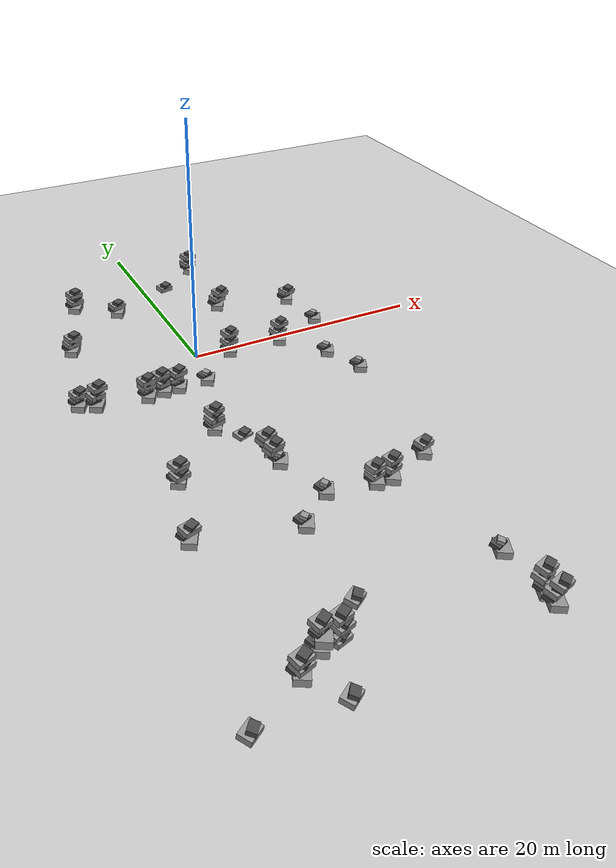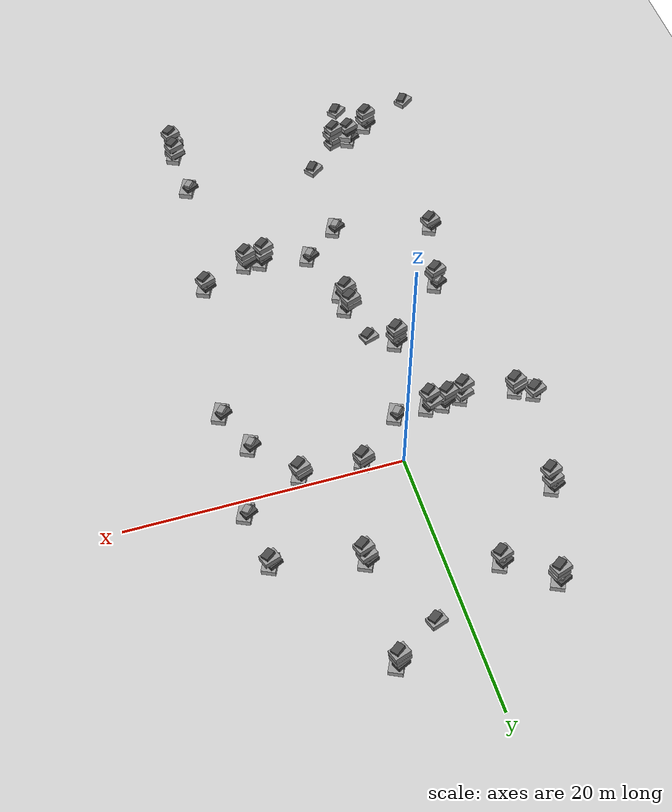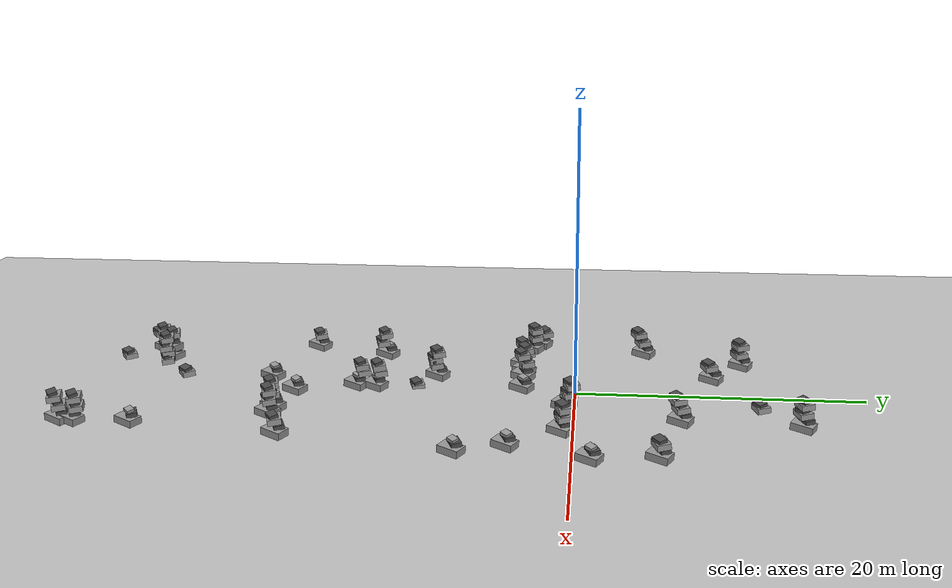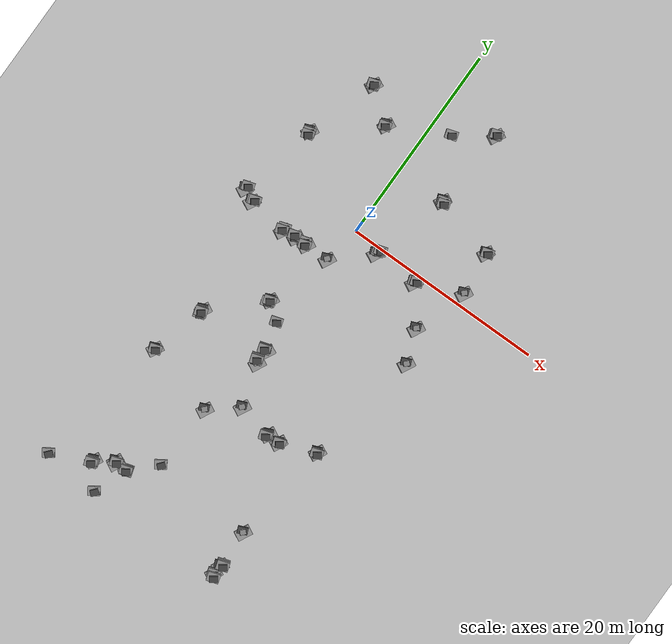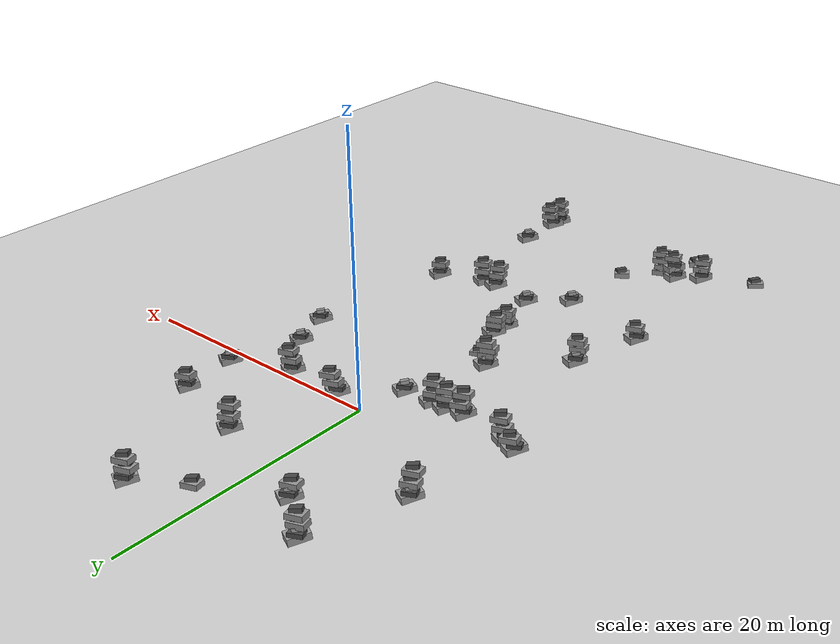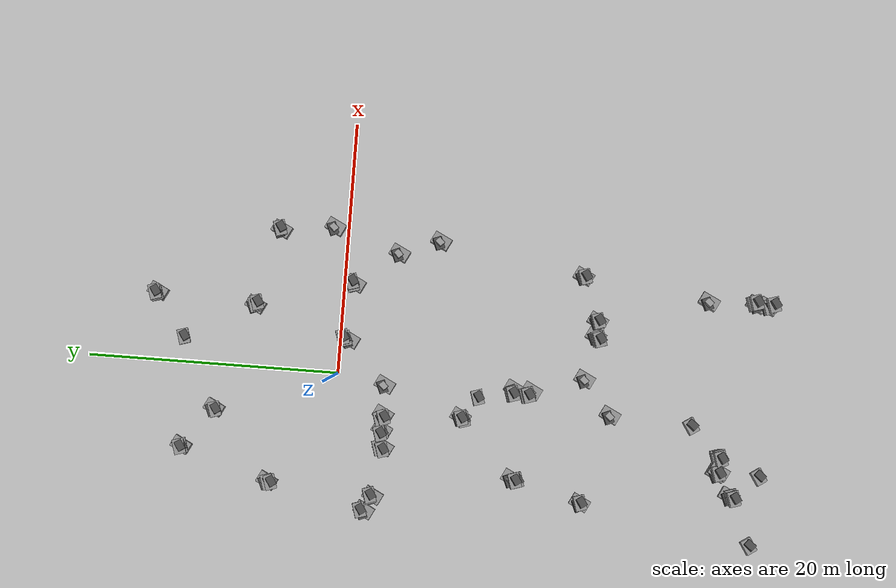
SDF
<sdf version="1.6">
 <world name="world">
  <gravity>0 0 -9.8</gravity>
  <physics default="0" name="default_physics" type="ode">
   <max_step_size>0.001</max_step_size>
   <real_time_factor>1</real_time_factor>
   <real_time_update_rate>1000</real_time_update_rate>
  </physics>
  <scene><ambient>0.6 0.6 0.6 1</ambient><background>0.4 0.4 0.4 1</background><shadows>false</shadows></scene>
  <include><uri>model://sun</uri></include>
  <include><uri>model://ground_plane</uri><pose>0 0 -0.1 0 -0 0</pose></include>
  <model name="rubble2_01">
   <static>1</static>
   <pose>-5.51736 -30.8139 0.704065 0 -0 0</pose>
   <link name="link">
    <collision name="base_collision">
     <pose>0 0 0.25 0.05 0.1 1.1</pose>
     <geometry><box><size>1.5 1 0.5</size></box></geometry>
    </collision>
    <visual name="base_visual">
     <pose>0 0 0.25 0.05 0.1 1.1</pose>
     <geometry><box><size>1.5 1 0.5</size></box></geometry>
     <material>
      <script><uri>file://media/materials/scripts/gazebo.material</uri><name>Gazebo/Grey</name></script>
     </material>
    </visual>
    <collision name="mid_collision">
     <pose>-0.2 0.2 0.6 0.15 0.05 0.4</pose>
     <geometry><box><size>1 0.7 0.3</size></box></geometry>
    </collision>
    <visual name="mid_visual">
     <pose>-0.2 0.2 0.6 0.15 0.05 0.4</pose>
     <geometry><box><size>1 0.7 0.3</size></box></geometry>
     <material>
      <script><uri>file://media/materials/scripts/gazebo.material</uri><name>Gazebo/DarkGrey</name></script>
     </material>
    </visual>
    <collision name="top_collision">
     <pose>-0.1 0.1 0.85 0.2 0.15 0.8</pose>
     <geometry><box><size>0.6 0.5 0.25</size></box></geometry>
    </collision>
    <visual name="top_visual">
     <pose>-0.1 0.1 0.85 0.2 0.15 0.8</pose>
     <geometry><box><size>0.6 0.5 0.25</size></box></geometry>
     <material>
      <script><uri>file://media/materials/scripts/gazebo.material</uri><name>Gazebo/Grey</name></script>
     </material>
    </visual>
   </link>
  </model>
  <model name="rubble1_01">
   <static>1</static>
   <pose>-4.6007 -30.7144 0.545113 0 -0 0</pose>
   <link name="link">
    <collision name="base_collision">
     <pose>0 0 0.2 0.1 0.05 0.3</pose>
     <geometry><box><size>1.2 0.9 0.4</size></box></geometry>
    </collision>
    <visual name="base_visual">
     <pose>0 0 0.2 0.1 0.05 0.3</pose>
     <geometry><box><size>1.2 0.9 0.4</size></box></geometry>
     <material>
      <script><uri>file://media/materials/scripts/gazebo.material</uri><name>Gazebo/Grey</name></script>
     </material>
    </visual>
    <collision name="top_collision">
     <pose>0.1 -0.1 0.5 0.2 0.1 0.6</pose>
     <geometry><box><size>0.8 0.6 0.3</size></box></geometry>
    </collision>
    <visual name="top_visual">
     <pose>0.1 -0.1 0.5 0.2 0.1 0.6</pose>
     <geometry><box><size>0.8 0.6 0.3</size></box></geometry>
     <material>
      <script><uri>file://media/materials/scripts/gazebo.material</uri><name>Gazebo/DarkGrey</name></script>
     </material>
    </visual>
   </link>
  </model>
  <model name="rubble1_02">
   <static>1</static>
   <pose>-4.41712 -30.6792 1.66266 0 -0 0</pose>
   <link name="link">
    <collision name="base_collision">
     <pose>0 0 0.2 0.1 0.05 0.3</pose>
     <geometry><box><size>1.2 0.9 0.4</size></box></geometry>
    </collision>
    <visual name="base_visual">
     <pose>0 0 0.2 0.1 0.05 0.3</pose>
     <geometry><box><size>1.2 0.9 0.4</size></box></geometry>
     <material>
      <script><uri>file://media/materials/scripts/gazebo.material</uri><name>Gazebo/Grey</name></script>
     </material>
    </visual>
    <collision name="top_collision">
     <pose>0.1 -0.1 0.5 0.2 0.1 0.6</pose>
     <geometry><box><size>0.8 0.6 0.3</size></box></geometry>
    </collision>
    <visual name="top_visual">
     <pose>0.1 -0.1 0.5 0.2 0.1 0.6</pose>
     <geometry><box><size>0.8 0.6 0.3</size></box></geometry>
     <material>
      <script><uri>file://media/materials/scripts/gazebo.material</uri><name>Gazebo/DarkGrey</name></script>
     </material>
    </visual>
   </link>
  </model>
  <model name="rubble2_02">
   <static>1</static>
   <pose>-7.42704 -31.9147 0 0 -0 0</pose>
   <link name="link">
    <collision name="base_collision">
     <pose>0 0 0.25 0.05 0.1 1.1</pose>
     <geometry><box><size>1.5 1 0.5</size></box></geometry>
    </collision>
    <visual name="base_visual">
     <pose>0 0 0.25 0.05 0.1 1.1</pose>
     <geometry><box><size>1.5 1 0.5</size></box></geometry>
     <material>
      <script><uri>file://media/materials/scripts/gazebo.material</uri><name>Gazebo/Grey</name></script>
     </material>
    </visual>
    <collision name="mid_collision">
     <pose>-0.2 0.2 0.6 0.15 0.05 0.4</pose>
     <geometry><box><size>1 0.7 0.3</size></box></geometry>
    </collision>
    <visual name="mid_visual">
     <pose>-0.2 0.2 0.6 0.15 0.05 0.4</pose>
     <geometry><box><size>1 0.7 0.3</size></box></geometry>
     <material>
      <script><uri>file://media/materials/scripts/gazebo.material</uri><name>Gazebo/DarkGrey</name></script>
     </material>
    </visual>
    <collision name="top_collision">
     <pose>-0.1 0.1 0.85 0.2 0.15 0.8</pose>
     <geometry><box><size>0.6 0.5 0.25</size></box></geometry>
    </collision>
    <visual name="top_visual">
     <pose>-0.1 0.1 0.85 0.2 0.15 0.8</pose>
     <geometry><box><size>0.6 0.5 0.25</size></box></geometry>
     <material>
      <script><uri>file://media/materials/scripts/gazebo.material</uri><name>Gazebo/Grey</name></script>
     </material>
    </visual>
   </link>
  </model>
  <model name="rubble1_03">
   <static>1</static>
   <pose>-7.51015 -31.9959 1.35527 0 -0 0</pose>
   <link name="link">
    <collision name="base_collision">
     <pose>0 0 0.2 0.1 0.05 0.3</pose>
     <geometry><box><size>1.2 0.9 0.4</size></box></geometry>
    </collision>
    <visual name="base_visual">
     <pose>0 0 0.2 0.1 0.05 0.3</pose>
     <geometry><box><size>1.2 0.9 0.4</size></box></geometry>
     <material>
      <script><uri>file://media/materials/scripts/gazebo.material</uri><name>Gazebo/Grey</name></script>
     </material>
    </visual>
    <collision name="top_collision">
     <pose>0.1 -0.1 0.5 0.2 0.1 0.6</pose>
     <geometry><box><size>0.8 0.6 0.3</size></box></geometry>
    </collision>
    <visual name="top_visual">
     <pose>0.1 -0.1 0.5 0.2 0.1 0.6</pose>
     <geometry><box><size>0.8 0.6 0.3</size></box></geometry>
     <material>
      <script><uri>file://media/materials/scripts/gazebo.material</uri><name>Gazebo/DarkGrey</name></script>
     </material>
    </visual>
   </link>
  </model>
  <model name="rubble1_04">
   <static>1</static>
   <pose>-7.44189 -31.9552 0.739677 0 -0 0</pose>
   <link name="link">
    <collision name="base_collision">
     <pose>0 0 0.2 0.1 0.05 0.3</pose>
     <geometry><box><size>1.2 0.9 0.4</size></box></geometry>
    </collision>
    <visual name="base_visual">
     <pose>0 0 0.2 0.1 0.05 0.3</pose>
     <geometry><box><size>1.2 0.9 0.4</size></box></geometry>
     <material>
      <script><uri>file://media/materials/scripts/gazebo.material</uri><name>Gazebo/Grey</name></script>
     </material>
    </visual>
    <collision name="top_collision">
     <pose>0.1 -0.1 0.5 0.2 0.1 0.6</pose>
     <geometry><box><size>0.8 0.6 0.3</size></box></geometry>
    </collision>
    <visual name="top_visual">
     <pose>0.1 -0.1 0.5 0.2 0.1 0.6</pose>
     <geometry><box><size>0.8 0.6 0.3</size></box></geometry>
     <material>
      <script><uri>file://media/materials/scripts/gazebo.material</uri><name>Gazebo/DarkGrey</name></script>
     </material>
    </visual>
   </link>
  </model>
  <model name="rubble2_03">
   <static>1</static>
   <pose>-2.72268 -10.0337 0 0 -0 0</pose>
   <link name="link">
    <collision name="base_collision">
     <pose>0 0 0.25 0.05 0.1 1.1</pose>
     <geometry><box><size>1.5 1 0.5</size></box></geometry>
    </collision>
    <visual name="base_visual">
     <pose>0 0 0.25 0.05 0.1 1.1</pose>
     <geometry><box><size>1.5 1 0.5</size></box></geometry>
     <material>
      <script><uri>file://media/materials/scripts/gazebo.material</uri><name>Gazebo/Grey</name></script>
     </material>
    </visual>
    <collision name="mid_collision">
     <pose>-0.2 0.2 0.6 0.15 0.05 0.4</pose>
     <geometry><box><size>1 0.7 0.3</size></box></geometry>
    </collision>
    <visual name="mid_visual">
     <pose>-0.2 0.2 0.6 0.15 0.05 0.4</pose>
     <geometry><box><size>1 0.7 0.3</size></box></geometry>
     <material>
      <script><uri>file://media/materials/scripts/gazebo.material</uri><name>Gazebo/DarkGrey</name></script>
     </material>
    </visual>
    <collision name="top_collision">
     <pose>-0.1 0.1 0.85 0.2 0.15 0.8</pose>
     <geometry><box><size>0.6 0.5 0.25</size></box></geometry>
    </collision>
    <visual name="top_visual">
     <pose>-0.1 0.1 0.85 0.2 0.15 0.8</pose>
     <geometry><box><size>0.6 0.5 0.25</size></box></geometry>
     <material>
      <script><uri>file://media/materials/scripts/gazebo.material</uri><name>Gazebo/Grey</name></script>
     </material>
    </visual>
   </link>
  </model>
  <model name="rubble1_05">
   <static>1</static>
   <pose>-2.87095 -10.2207 1.15439 0 -0 0</pose>
   <link name="link">
    <collision name="base_collision">
     <pose>0 0 0.2 0.1 0.05 0.3</pose>
     <geometry><box><size>1.2 0.9 0.4</size></box></geometry>
    </collision>
    <visual name="base_visual">
     <pose>0 0 0.2 0.1 0.05 0.3</pose>
     <geometry><box><size>1.2 0.9 0.4</size></box></geometry>
     <material>
      <script><uri>file://media/materials/scripts/gazebo.material</uri><name>Gazebo/Grey</name></script>
     </material>
    </visual>
    <collision name="top_collision">
     <pose>0.1 -0.1 0.5 0.2 0.1 0.6</pose>
     <geometry><box><size>0.8 0.6 0.3</size></box></geometry>
    </collision>
    <visual name="top_visual">
     <pose>0.1 -0.1 0.5 0.2 0.1 0.6</pose>
     <geometry><box><size>0.8 0.6 0.3</size></box></geometry>
     <material>
      <script><uri>file://media/materials/scripts/gazebo.material</uri><name>Gazebo/DarkGrey</name></script>
     </material>
    </visual>
   </link>
  </model>
  <model name="rubble2_04">
   <static>1</static>
   <pose>2.77458 -0.70412 0 0 -0 0</pose>
   <link name="link">
    <collision name="base_collision">
     <pose>0 0 0.25 0.05 0.1 1.1</pose>
     <geometry><box><size>1.5 1 0.5</size></box></geometry>
    </collision>
    <visual name="base_visual">
     <pose>0 0 0.25 0.05 0.1 1.1</pose>
     <geometry><box><size>1.5 1 0.5</size></box></geometry>
     <material>
      <script><uri>file://media/materials/scripts/gazebo.material</uri><name>Gazebo/Grey</name></script>
     </material>
    </visual>
    <collision name="mid_collision">
     <pose>-0.2 0.2 0.6 0.15 0.05 0.4</pose>
     <geometry><box><size>1 0.7 0.3</size></box></geometry>
    </collision>
    <visual name="mid_visual">
     <pose>-0.2 0.2 0.6 0.15 0.05 0.4</pose>
     <geometry><box><size>1 0.7 0.3</size></box></geometry>
     <material>
      <script><uri>file://media/materials/scripts/gazebo.material</uri><name>Gazebo/DarkGrey</name></script>
     </material>
    </visual>
    <collision name="top_collision">
     <pose>-0.1 0.1 0.85 0.2 0.15 0.8</pose>
     <geometry><box><size>0.6 0.5 0.25</size></box></geometry>
    </collision>
    <visual name="top_visual">
     <pose>-0.1 0.1 0.85 0.2 0.15 0.8</pose>
     <geometry><box><size>0.6 0.5 0.25</size></box></geometry>
     <material>
      <script><uri>file://media/materials/scripts/gazebo.material</uri><name>Gazebo/Grey</name></script>
     </material>
    </visual>
   </link>
  </model>
  <model name="rubble1_06">
   <static>1</static>
   <pose>2.80754 -0.369767 0.854105 0 -0 0</pose>
   <link name="link">
    <collision name="base_collision">
     <pose>0 0 0.2 0.1 0.05 0.3</pose>
     <geometry><box><size>1.2 0.9 0.4</size></box></geometry>
    </collision>
    <visual name="base_visual">
     <pose>0 0 0.2 0.1 0.05 0.3</pose>
     <geometry><box><size>1.2 0.9 0.4</size></box></geometry>
     <material>
      <script><uri>file://media/materials/scripts/gazebo.material</uri><name>Gazebo/Grey</name></script>
     </material>
    </visual>
    <collision name="top_collision">
     <pose>0.1 -0.1 0.5 0.2 0.1 0.6</pose>
     <geometry><box><size>0.8 0.6 0.3</size></box></geometry>
    </collision>
    <visual name="top_visual">
     <pose>0.1 -0.1 0.5 0.2 0.1 0.6</pose>
     <geometry><box><size>0.8 0.6 0.3</size></box></geometry>
     <material>
      <script><uri>file://media/materials/scripts/gazebo.material</uri><name>Gazebo/DarkGrey</name></script>
     </material>
    </visual>
   </link>
  </model>
  <model name="rubble2_05">
   <static>1</static>
   <pose>5 7 0 0 -0 0</pose>
   <link name="link">
    <collision name="base_collision">
     <pose>0 0 0.25 0.05 0.1 1.1</pose>
     <geometry><box><size>1.5 1 0.5</size></box></geometry>
    </collision>
    <visual name="base_visual">
     <pose>0 0 0.25 0.05 0.1 1.1</pose>
     <geometry><box><size>1.5 1 0.5</size></box></geometry>
     <material>
      <script><uri>file://media/materials/scripts/gazebo.material</uri><name>Gazebo/Grey</name></script>
     </material>
    </visual>
    <collision name="mid_collision">
     <pose>-0.2 0.2 0.6 0.15 0.05 0.4</pose>
     <geometry><box><size>1 0.7 0.3</size></box></geometry>
    </collision>
    <visual name="mid_visual">
     <pose>-0.2 0.2 0.6 0.15 0.05 0.4</pose>
     <geometry><box><size>1 0.7 0.3</size></box></geometry>
     <material>
      <script><uri>file://media/materials/scripts/gazebo.material</uri><name>Gazebo/DarkGrey</name></script>
     </material>
    </visual>
    <collision name="top_collision">
     <pose>-0.1 0.1 0.85 0.2 0.15 0.8</pose>
     <geometry><box><size>0.6 0.5 0.25</size></box></geometry>
    </collision>
    <visual name="top_visual">
     <pose>-0.1 0.1 0.85 0.2 0.15 0.8</pose>
     <geometry><box><size>0.6 0.5 0.25</size></box></geometry>
     <material>
      <script><uri>file://media/materials/scripts/gazebo.material</uri><name>Gazebo/Grey</name></script>
     </material>
    </visual>
   </link>
  </model>
  <model name="rubble2_06">
   <static>1</static>
   <pose>-5.60363 -4.04821 0 0 -0 0</pose>
   <link name="link">
    <collision name="base_collision">
     <pose>0 0 0.25 0.05 0.1 1.1</pose>
     <geometry><box><size>1.5 1 0.5</size></box></geometry>
    </collision>
    <visual name="base_visual">
     <pose>0 0 0.25 0.05 0.1 1.1</pose>
     <geometry><box><size>1.5 1 0.5</size></box></geometry>
     <material>
      <script><uri>file://media/materials/scripts/gazebo.material</uri><name>Gazebo/Grey</name></script>
     </material>
    </visual>
    <collision name="mid_collision">
     <pose>-0.2 0.2 0.6 0.15 0.05 0.4</pose>
     <geometry><box><size>1 0.7 0.3</size></box></geometry>
    </collision>
    <visual name="mid_visual">
     <pose>-0.2 0.2 0.6 0.15 0.05 0.4</pose>
     <geometry><box><size>1 0.7 0.3</size></box></geometry>
     <material>
      <script><uri>file://media/materials/scripts/gazebo.material</uri><name>Gazebo/DarkGrey</name></script>
     </material>
    </visual>
    <collision name="top_collision">
     <pose>-0.1 0.1 0.85 0.2 0.15 0.8</pose>
     <geometry><box><size>0.6 0.5 0.25</size></box></geometry>
    </collision>
    <visual name="top_visual">
     <pose>-0.1 0.1 0.85 0.2 0.15 0.8</pose>
     <geometry><box><size>0.6 0.5 0.25</size></box></geometry>
     <material>
      <script><uri>file://media/materials/scripts/gazebo.material</uri><name>Gazebo/Grey</name></script>
     </material>
    </visual>
   </link>
  </model>
  <model name="rubble2_07">
   <static>1</static>
   <pose>-4.21594 -3.83818 0 0 -0 0</pose>
   <link name="link">
    <collision name="base_collision">
     <pose>0 0 0.25 0.05 0.1 1.1</pose>
     <geometry><box><size>1.5 1 0.5</size></box></geometry>
    </collision>
    <visual name="base_visual">
     <pose>0 0 0.25 0.05 0.1 1.1</pose>
     <geometry><box><size>1.5 1 0.5</size></box></geometry>
     <material>
      <script><uri>file://media/materials/scripts/gazebo.material</uri><name>Gazebo/Grey</name></script>
     </material>
    </visual>
    <collision name="mid_collision">
     <pose>-0.2 0.2 0.6 0.15 0.05 0.4</pose>
     <geometry><box><size>1 0.7 0.3</size></box></geometry>
    </collision>
    <visual name="mid_visual">
     <pose>-0.2 0.2 0.6 0.15 0.05 0.4</pose>
     <geometry><box><size>1 0.7 0.3</size></box></geometry>
     <material>
      <script><uri>file://media/materials/scripts/gazebo.material</uri><name>Gazebo/DarkGrey</name></script>
     </material>
    </visual>
    <collision name="top_collision">
     <pose>-0.1 0.1 0.85 0.2 0.15 0.8</pose>
     <geometry><box><size>0.6 0.5 0.25</size></box></geometry>
    </collision>
    <visual name="top_visual">
     <pose>-0.1 0.1 0.85 0.2 0.15 0.8</pose>
     <geometry><box><size>0.6 0.5 0.25</size></box></geometry>
     <material>
      <script><uri>file://media/materials/scripts/gazebo.material</uri><name>Gazebo/Grey</name></script>
     </material>
    </visual>
   </link>
  </model>
  <model name="rubble2_08">
   <static>1</static>
   <pose>-2.99667 -3.84545 0 0 -0 0</pose>
   <link name="link">
    <collision name="base_collision">
     <pose>0 0 0.25 0.05 0.1 1.1</pose>
     <geometry><box><size>1.5 1 0.5</size></box></geometry>
    </collision>
    <visual name="base_visual">
     <pose>0 0 0.25 0.05 0.1 1.1</pose>
     <geometry><box><size>1.5 1 0.5</size></box></geometry>
     <material>
      <script><uri>file://media/materials/scripts/gazebo.material</uri><name>Gazebo/Grey</name></script>
     </material>
    </visual>
    <collision name="mid_collision">
     <pose>-0.2 0.2 0.6 0.15 0.05 0.4</pose>
     <geometry><box><size>1 0.7 0.3</size></box></geometry>
    </collision>
    <visual name="mid_visual">
     <pose>-0.2 0.2 0.6 0.15 0.05 0.4</pose>
     <geometry><box><size>1 0.7 0.3</size></box></geometry>
     <material>
      <script><uri>file://media/materials/scripts/gazebo.material</uri><name>Gazebo/DarkGrey</name></script>
     </material>
    </visual>
    <collision name="top_collision">
     <pose>-0.1 0.1 0.85 0.2 0.15 0.8</pose>
     <geometry><box><size>0.6 0.5 0.25</size></box></geometry>
    </collision>
    <visual name="top_visual">
     <pose>-0.1 0.1 0.85 0.2 0.15 0.8</pose>
     <geometry><box><size>0.6 0.5 0.25</size></box></geometry>
     <material>
      <script><uri>file://media/materials/scripts/gazebo.material</uri><name>Gazebo/Grey</name></script>
     </material>
    </visual>
   </link>
  </model>
  <model name="rubble2_09">
   <static>1</static>
   <pose>11.1684 5.37063 0 0 -0 0</pose>
   <link name="link">
    <collision name="base_collision">
     <pose>0 0 0.25 0.05 0.1 1.1</pose>
     <geometry><box><size>1.5 1 0.5</size></box></geometry>
    </collision>
    <visual name="base_visual">
     <pose>0 0 0.25 0.05 0.1 1.1</pose>
     <geometry><box><size>1.5 1 0.5</size></box></geometry>
     <material>
      <script><uri>file://media/materials/scripts/gazebo.material</uri><name>Gazebo/Grey</name></script>
     </material>
    </visual>
    <collision name="mid_collision">
     <pose>-0.2 0.2 0.6 0.15 0.05 0.4</pose>
     <geometry><box><size>1 0.7 0.3</size></box></geometry>
    </collision>
    <visual name="mid_visual">
     <pose>-0.2 0.2 0.6 0.15 0.05 0.4</pose>
     <geometry><box><size>1 0.7 0.3</size></box></geometry>
     <material>
      <script><uri>file://media/materials/scripts/gazebo.material</uri><name>Gazebo/DarkGrey</name></script>
     </material>
    </visual>
    <collision name="top_collision">
     <pose>-0.1 0.1 0.85 0.2 0.15 0.8</pose>
     <geometry><box><size>0.6 0.5 0.25</size></box></geometry>
    </collision>
    <visual name="top_visual">
     <pose>-0.1 0.1 0.85 0.2 0.15 0.8</pose>
     <geometry><box><size>0.6 0.5 0.25</size></box></geometry>
     <material>
      <script><uri>file://media/materials/scripts/gazebo.material</uri><name>Gazebo/Grey</name></script>
     </material>
    </visual>
   </link>
  </model>
  <model name="rubble2_10">
   <static>1</static>
   <pose>-3.4664 9.69034 0 0 -0 0</pose>
   <link name="link">
    <collision name="base_collision">
     <pose>0 0 0.25 0.05 0.1 1.1</pose>
     <geometry><box><size>1.5 1 0.5</size></box></geometry>
    </collision>
    <visual name="base_visual">
     <pose>0 0 0.25 0.05 0.1 1.1</pose>
     <geometry><box><size>1.5 1 0.5</size></box></geometry>
     <material>
      <script><uri>file://media/materials/scripts/gazebo.material</uri><name>Gazebo/Grey</name></script>
     </material>
    </visual>
    <collision name="mid_collision">
     <pose>-0.2 0.2 0.6 0.15 0.05 0.4</pose>
     <geometry><box><size>1 0.7 0.3</size></box></geometry>
    </collision>
    <visual name="mid_visual">
     <pose>-0.2 0.2 0.6 0.15 0.05 0.4</pose>
     <geometry><box><size>1 0.7 0.3</size></box></geometry>
     <material>
      <script><uri>file://media/materials/scripts/gazebo.material</uri><name>Gazebo/DarkGrey</name></script>
     </material>
    </visual>
    <collision name="top_collision">
     <pose>-0.1 0.1 0.85 0.2 0.15 0.8</pose>
     <geometry><box><size>0.6 0.5 0.25</size></box></geometry>
    </collision>
    <visual name="top_visual">
     <pose>-0.1 0.1 0.85 0.2 0.15 0.8</pose>
     <geometry><box><size>0.6 0.5 0.25</size></box></geometry>
     <material>
      <script><uri>file://media/materials/scripts/gazebo.material</uri><name>Gazebo/Grey</name></script>
     </material>
    </visual>
   </link>
  </model>
  <model name="rubble2_11">
   <static>1</static>
   <pose>9.22413 -19.0507 0 0 -0 0</pose>
   <link name="link">
    <collision name="base_collision">
     <pose>0 0 0.25 0.05 0.1 1.1</pose>
     <geometry><box><size>1.5 1 0.5</size></box></geometry>
    </collision>
    <visual name="base_visual">
     <pose>0 0 0.25 0.05 0.1 1.1</pose>
     <geometry><box><size>1.5 1 0.5</size></box></geometry>
     <material>
      <script><uri>file://media/materials/scripts/gazebo.material</uri><name>Gazebo/Grey</name></script>
     </material>
    </visual>
    <collision name="mid_collision">
     <pose>-0.2 0.2 0.6 0.15 0.05 0.4</pose>
     <geometry><box><size>1 0.7 0.3</size></box></geometry>
    </collision>
    <visual name="mid_visual">
     <pose>-0.2 0.2 0.6 0.15 0.05 0.4</pose>
     <geometry><box><size>1 0.7 0.3</size></box></geometry>
     <material>
      <script><uri>file://media/materials/scripts/gazebo.material</uri><name>Gazebo/DarkGrey</name></script>
     </material>
    </visual>
    <collision name="top_collision">
     <pose>-0.1 0.1 0.85 0.2 0.15 0.8</pose>
     <geometry><box><size>0.6 0.5 0.25</size></box></geometry>
    </collision>
    <visual name="top_visual">
     <pose>-0.1 0.1 0.85 0.2 0.15 0.8</pose>
     <geometry><box><size>0.6 0.5 0.25</size></box></geometry>
     <material>
      <script><uri>file://media/materials/scripts/gazebo.material</uri><name>Gazebo/Grey</name></script>
     </material>
    </visual>
   </link>
  </model>
  <model name="rubble2_12">
   <static>1</static>
   <pose>-7.31682 -14.4503 0 0 -0 0</pose>
   <link name="link">
    <collision name="base_collision">
     <pose>0 0 0.25 0.05 0.1 1.1</pose>
     <geometry><box><size>1.5 1 0.5</size></box></geometry>
    </collision>
    <visual name="base_visual">
     <pose>0 0 0.25 0.05 0.1 1.1</pose>
     <geometry><box><size>1.5 1 0.5</size></box></geometry>
     <material>
      <script><uri>file://media/materials/scripts/gazebo.material</uri><name>Gazebo/Grey</name></script>
     </material>
    </visual>
    <collision name="mid_collision">
     <pose>-0.2 0.2 0.6 0.15 0.05 0.4</pose>
     <geometry><box><size>1 0.7 0.3</size></box></geometry>
    </collision>
    <visual name="mid_visual">
     <pose>-0.2 0.2 0.6 0.15 0.05 0.4</pose>
     <geometry><box><size>1 0.7 0.3</size></box></geometry>
     <material>
      <script><uri>file://media/materials/scripts/gazebo.material</uri><name>Gazebo/DarkGrey</name></script>
     </material>
    </visual>
    <collision name="top_collision">
     <pose>-0.1 0.1 0.85 0.2 0.15 0.8</pose>
     <geometry><box><size>0.6 0.5 0.25</size></box></geometry>
    </collision>
    <visual name="top_visual">
     <pose>-0.1 0.1 0.85 0.2 0.15 0.8</pose>
     <geometry><box><size>0.6 0.5 0.25</size></box></geometry>
     <material>
      <script><uri>file://media/materials/scripts/gazebo.material</uri><name>Gazebo/Grey</name></script>
     </material>
    </visual>
   </link>
  </model>
  <model name="rubble1_07">
   <static>1</static>
   <pose>4.98706 6.99691 0.854105 0 -0 0</pose>
   <link name="link">
    <collision name="base_collision">
     <pose>0 0 0.2 0.1 0.05 0.3</pose>
     <geometry><box><size>1.2 0.9 0.4</size></box></geometry>
    </collision>
    <visual name="base_visual">
     <pose>0 0 0.2 0.1 0.05 0.3</pose>
     <geometry><box><size>1.2 0.9 0.4</size></box></geometry>
     <material>
      <script><uri>file://media/materials/scripts/gazebo.material</uri><name>Gazebo/Grey</name></script>
     </material>
    </visual>
    <collision name="top_collision">
     <pose>0.1 -0.1 0.5 0.2 0.1 0.6</pose>
     <geometry><box><size>0.8 0.6 0.3</size></box></geometry>
    </collision>
    <visual name="top_visual">
     <pose>0.1 -0.1 0.5 0.2 0.1 0.6</pose>
     <geometry><box><size>0.8 0.6 0.3</size></box></geometry>
     <material>
      <script><uri>file://media/materials/scripts/gazebo.material</uri><name>Gazebo/DarkGrey</name></script>
     </material>
    </visual>
   </link>
  </model>
  <model name="rubble1_08">
   <static>1</static>
   <pose>-3.56729 9.54904 0.854105 0 -0 0</pose>
   <link name="link">
    <collision name="base_collision">
     <pose>0 0 0.2 0.1 0.05 0.3</pose>
     <geometry><box><size>1.2 0.9 0.4</size></box></geometry>
    </collision>
    <visual name="base_visual">
     <pose>0 0 0.2 0.1 0.05 0.3</pose>
     <geometry><box><size>1.2 0.9 0.4</size></box></geometry>
     <material>
      <script><uri>file://media/materials/scripts/gazebo.material</uri><name>Gazebo/Grey</name></script>
     </material>
    </visual>
    <collision name="top_collision">
     <pose>0.1 -0.1 0.5 0.2 0.1 0.6</pose>
     <geometry><box><size>0.8 0.6 0.3</size></box></geometry>
    </collision>
    <visual name="top_visual">
     <pose>0.1 -0.1 0.5 0.2 0.1 0.6</pose>
     <geometry><box><size>0.8 0.6 0.3</size></box></geometry>
     <material>
      <script><uri>file://media/materials/scripts/gazebo.material</uri><name>Gazebo/DarkGrey</name></script>
     </material>
    </visual>
   </link>
  </model>
  <model name="rubble1_09">
   <static>1</static>
   <pose>-5.63108 -3.68594 0.854105 0 -0 0</pose>
   <link name="link">
    <collision name="base_collision">
     <pose>0 0 0.2 0.1 0.05 0.3</pose>
     <geometry><box><size>1.2 0.9 0.4</size></box></geometry>
    </collision>
    <visual name="base_visual">
     <pose>0 0 0.2 0.1 0.05 0.3</pose>
     <geometry><box><size>1.2 0.9 0.4</size></box></geometry>
     <material>
      <script><uri>file://media/materials/scripts/gazebo.material</uri><name>Gazebo/Grey</name></script>
     </material>
    </visual>
    <collision name="top_collision">
     <pose>0.1 -0.1 0.5 0.2 0.1 0.6</pose>
     <geometry><box><size>0.8 0.6 0.3</size></box></geometry>
    </collision>
    <visual name="top_visual">
     <pose>0.1 -0.1 0.5 0.2 0.1 0.6</pose>
     <geometry><box><size>0.8 0.6 0.3</size></box></geometry>
     <material>
      <script><uri>file://media/materials/scripts/gazebo.material</uri><name>Gazebo/DarkGrey</name></script>
     </material>
    </visual>
   </link>
  </model>
  <model name="rubble1_10">
   <static>1</static>
   <pose>-4.36239 -3.80436 0.854105 0 -0 0</pose>
   <link name="link">
    <collision name="base_collision">
     <pose>0 0 0.2 0.1 0.05 0.3</pose>
     <geometry><box><size>1.2 0.9 0.4</size></box></geometry>
    </collision>
    <visual name="base_visual">
     <pose>0 0 0.2 0.1 0.05 0.3</pose>
     <geometry><box><size>1.2 0.9 0.4</size></box></geometry>
     <material>
      <script><uri>file://media/materials/scripts/gazebo.material</uri><name>Gazebo/Grey</name></script>
     </material>
    </visual>
    <collision name="top_collision">
     <pose>0.1 -0.1 0.5 0.2 0.1 0.6</pose>
     <geometry><box><size>0.8 0.6 0.3</size></box></geometry>
    </collision>
    <visual name="top_visual">
     <pose>0.1 -0.1 0.5 0.2 0.1 0.6</pose>
     <geometry><box><size>0.8 0.6 0.3</size></box></geometry>
     <material>
      <script><uri>file://media/materials/scripts/gazebo.material</uri><name>Gazebo/DarkGrey</name></script>
     </material>
    </visual>
   </link>
  </model>
  <model name="rubble1_11">
   <static>1</static>
   <pose>-3.3633 -3.61102 0.854105 0 -0 0</pose>
   <link name="link">
    <collision name="base_collision">
     <pose>0 0 0.2 0.1 0.05 0.3</pose>
     <geometry><box><size>1.2 0.9 0.4</size></box></geometry>
    </collision>
    <visual name="base_visual">
     <pose>0 0 0.2 0.1 0.05 0.3</pose>
     <geometry><box><size>1.2 0.9 0.4</size></box></geometry>
     <material>
      <script><uri>file://media/materials/scripts/gazebo.material</uri><name>Gazebo/Grey</name></script>
     </material>
    </visual>
    <collision name="top_collision">
     <pose>0.1 -0.1 0.5 0.2 0.1 0.6</pose>
     <geometry><box><size>0.8 0.6 0.3</size></box></geometry>
    </collision>
    <visual name="top_visual">
     <pose>0.1 -0.1 0.5 0.2 0.1 0.6</pose>
     <geometry><box><size>0.8 0.6 0.3</size></box></geometry>
     <material>
      <script><uri>file://media/materials/scripts/gazebo.material</uri><name>Gazebo/DarkGrey</name></script>
     </material>
    </visual>
   </link>
  </model>
  <model name="rubble2_13">
   <static>1</static>
   <pose>-0.248679 -15.565 0 0 -0 0</pose>
   <link name="link">
    <collision name="base_collision">
     <pose>0 0 0.25 0.05 0.1 1.1</pose>
     <geometry><box><size>1.5 1 0.5</size></box></geometry>
    </collision>
    <visual name="base_visual">
     <pose>0 0 0.25 0.05 0.1 1.1</pose>
     <geometry><box><size>1.5 1 0.5</size></box></geometry>
     <material>
      <script><uri>file://media/materials/scripts/gazebo.material</uri><name>Gazebo/Grey</name></script>
     </material>
    </visual>
    <collision name="mid_collision">
     <pose>-0.2 0.2 0.6 0.15 0.05 0.4</pose>
     <geometry><box><size>1 0.7 0.3</size></box></geometry>
    </collision>
    <visual name="mid_visual">
     <pose>-0.2 0.2 0.6 0.15 0.05 0.4</pose>
     <geometry><box><size>1 0.7 0.3</size></box></geometry>
     <material>
      <script><uri>file://media/materials/scripts/gazebo.material</uri><name>Gazebo/DarkGrey</name></script>
     </material>
    </visual>
    <collision name="top_collision">
     <pose>-0.1 0.1 0.85 0.2 0.15 0.8</pose>
     <geometry><box><size>0.6 0.5 0.25</size></box></geometry>
    </collision>
    <visual name="top_visual">
     <pose>-0.1 0.1 0.85 0.2 0.15 0.8</pose>
     <geometry><box><size>0.6 0.5 0.25</size></box></geometry>
     <material>
      <script><uri>file://media/materials/scripts/gazebo.material</uri><name>Gazebo/Grey</name></script>
     </material>
    </visual>
   </link>
  </model>
  <model name="rubble2_14">
   <static>1</static>
   <pose>-0.190508 -14.1517 0 0 -0 0</pose>
   <link name="link">
    <collision name="base_collision">
     <pose>0 0 0.25 0.05 0.1 1.1</pose>
     <geometry><box><size>1.5 1 0.5</size></box></geometry>
    </collision>
    <visual name="base_visual">
     <pose>0 0 0.25 0.05 0.1 1.1</pose>
     <geometry><box><size>1.5 1 0.5</size></box></geometry>
     <material>
      <script><uri>file://media/materials/scripts/gazebo.material</uri><name>Gazebo/Grey</name></script>
     </material>
    </visual>
    <collision name="mid_collision">
     <pose>-0.2 0.2 0.6 0.15 0.05 0.4</pose>
     <geometry><box><size>1 0.7 0.3</size></box></geometry>
    </collision>
    <visual name="mid_visual">
     <pose>-0.2 0.2 0.6 0.15 0.05 0.4</pose>
     <geometry><box><size>1 0.7 0.3</size></box></geometry>
     <material>
      <script><uri>file://media/materials/scripts/gazebo.material</uri><name>Gazebo/DarkGrey</name></script>
     </material>
    </visual>
    <collision name="top_collision">
     <pose>-0.1 0.1 0.85 0.2 0.15 0.8</pose>
     <geometry><box><size>0.6 0.5 0.25</size></box></geometry>
    </collision>
    <visual name="top_visual">
     <pose>-0.1 0.1 0.85 0.2 0.15 0.8</pose>
     <geometry><box><size>0.6 0.5 0.25</size></box></geometry>
     <material>
      <script><uri>file://media/materials/scripts/gazebo.material</uri><name>Gazebo/Grey</name></script>
     </material>
    </visual>
   </link>
  </model>
  <model name="rubble1_12">
   <static>1</static>
   <pose>-0.54765 -15.1975 1.30082 0 -0 0</pose>
   <link name="link">
    <collision name="base_collision">
     <pose>0 0 0.2 0.1 0.05 0.3</pose>
     <geometry><box><size>1.2 0.9 0.4</size></box></geometry>
    </collision>
    <visual name="base_visual">
     <pose>0 0 0.2 0.1 0.05 0.3</pose>
     <geometry><box><size>1.2 0.9 0.4</size></box></geometry>
     <material>
      <script><uri>file://media/materials/scripts/gazebo.material</uri><name>Gazebo/Grey</name></script>
     </material>
    </visual>
    <collision name="top_collision">
     <pose>0.1 -0.1 0.5 0.2 0.1 0.6</pose>
     <geometry><box><size>0.8 0.6 0.3</size></box></geometry>
    </collision>
    <visual name="top_visual">
     <pose>0.1 -0.1 0.5 0.2 0.1 0.6</pose>
     <geometry><box><size>0.8 0.6 0.3</size></box></geometry>
     <material>
      <script><uri>file://media/materials/scripts/gazebo.material</uri><name>Gazebo/DarkGrey</name></script>
     </material>
    </visual>
   </link>
  </model>
  <model name="rubble1_13">
   <static>1</static>
   <pose>-0.531983 -13.9777 1.2937 0 -0 0</pose>
   <link name="link">
    <collision name="base_collision">
     <pose>0 0 0.2 0.1 0.05 0.3</pose>
     <geometry><box><size>1.2 0.9 0.4</size></box></geometry>
    </collision>
    <visual name="base_visual">
     <pose>0 0 0.2 0.1 0.05 0.3</pose>
     <geometry><box><size>1.2 0.9 0.4</size></box></geometry>
     <material>
      <script><uri>file://media/materials/scripts/gazebo.material</uri><name>Gazebo/Grey</name></script>
     </material>
    </visual>
    <collision name="top_collision">
     <pose>0.1 -0.1 0.5 0.2 0.1 0.6</pose>
     <geometry><box><size>0.8 0.6 0.3</size></box></geometry>
    </collision>
    <visual name="top_visual">
     <pose>0.1 -0.1 0.5 0.2 0.1 0.6</pose>
     <geometry><box><size>0.8 0.6 0.3</size></box></geometry>
     <material>
      <script><uri>file://media/materials/scripts/gazebo.material</uri><name>Gazebo/DarkGrey</name></script>
     </material>
    </visual>
   </link>
  </model>
  <model name="rubble2_15">
   <static>1</static>
   <pose>7.27639 -0.833168 0 0 -0 0</pose>
   <link name="link">
    <collision name="base_collision">
     <pose>0 0 0.25 0.05 0.1 1.1</pose>
     <geometry><box><size>1.5 1 0.5</size></box></geometry>
    </collision>
    <visual name="base_visual">
     <pose>0 0 0.25 0.05 0.1 1.1</pose>
     <geometry><box><size>1.5 1 0.5</size></box></geometry>
     <material>
      <script><uri>file://media/materials/scripts/gazebo.material</uri><name>Gazebo/Grey</name></script>
     </material>
    </visual>
    <collision name="mid_collision">
     <pose>-0.2 0.2 0.6 0.15 0.05 0.4</pose>
     <geometry><box><size>1 0.7 0.3</size></box></geometry>
    </collision>
    <visual name="mid_visual">
     <pose>-0.2 0.2 0.6 0.15 0.05 0.4</pose>
     <geometry><box><size>1 0.7 0.3</size></box></geometry>
     <material>
      <script><uri>file://media/materials/scripts/gazebo.material</uri><name>Gazebo/DarkGrey</name></script>
     </material>
    </visual>
    <collision name="top_collision">
     <pose>-0.1 0.1 0.85 0.2 0.15 0.8</pose>
     <geometry><box><size>0.6 0.5 0.25</size></box></geometry>
    </collision>
    <visual name="top_visual">
     <pose>-0.1 0.1 0.85 0.2 0.15 0.8</pose>
     <geometry><box><size>0.6 0.5 0.25</size></box></geometry>
     <material>
      <script><uri>file://media/materials/scripts/gazebo.material</uri><name>Gazebo/Grey</name></script>
     </material>
    </visual>
   </link>
  </model>
  <model name="rubble2_16">
   <static>1</static>
   <pose>-10.7362 -2.88621 0 0 -0 0</pose>
   <link name="link">
    <collision name="base_collision">
     <pose>0 0 0.25 0.05 0.1 1.1</pose>
     <geometry><box><size>1.5 1 0.5</size></box></geometry>
    </collision>
    <visual name="base_visual">
     <pose>0 0 0.25 0.05 0.1 1.1</pose>
     <geometry><box><size>1.5 1 0.5</size></box></geometry>
     <material>
      <script><uri>file://media/materials/scripts/gazebo.material</uri><name>Gazebo/Grey</name></script>
     </material>
    </visual>
    <collision name="mid_collision">
     <pose>-0.2 0.2 0.6 0.15 0.05 0.4</pose>
     <geometry><box><size>1 0.7 0.3</size></box></geometry>
    </collision>
    <visual name="mid_visual">
     <pose>-0.2 0.2 0.6 0.15 0.05 0.4</pose>
     <geometry><box><size>1 0.7 0.3</size></box></geometry>
     <material>
      <script><uri>file://media/materials/scripts/gazebo.material</uri><name>Gazebo/DarkGrey</name></script>
     </material>
    </visual>
    <collision name="top_collision">
     <pose>-0.1 0.1 0.85 0.2 0.15 0.8</pose>
     <geometry><box><size>0.6 0.5 0.25</size></box></geometry>
    </collision>
    <visual name="top_visual">
     <pose>-0.1 0.1 0.85 0.2 0.15 0.8</pose>
     <geometry><box><size>0.6 0.5 0.25</size></box></geometry>
     <material>
      <script><uri>file://media/materials/scripts/gazebo.material</uri><name>Gazebo/Grey</name></script>
     </material>
    </visual>
   </link>
  </model>
  <model name="rubble2_17">
   <static>1</static>
   <pose>-9.53296 -3.48983 0 0 -0 0</pose>
   <link name="link">
    <collision name="base_collision">
     <pose>0 0 0.25 0.05 0.1 1.1</pose>
     <geometry><box><size>1.5 1 0.5</size></box></geometry>
    </collision>
    <visual name="base_visual">
     <pose>0 0 0.25 0.05 0.1 1.1</pose>
     <geometry><box><size>1.5 1 0.5</size></box></geometry>
     <material>
      <script><uri>file://media/materials/scripts/gazebo.material</uri><name>Gazebo/Grey</name></script>
     </material>
    </visual>
    <collision name="mid_collision">
     <pose>-0.2 0.2 0.6 0.15 0.05 0.4</pose>
     <geometry><box><size>1 0.7 0.3</size></box></geometry>
    </collision>
    <visual name="mid_visual">
     <pose>-0.2 0.2 0.6 0.15 0.05 0.4</pose>
     <geometry><box><size>1 0.7 0.3</size></box></geometry>
     <material>
      <script><uri>file://media/materials/scripts/gazebo.material</uri><name>Gazebo/DarkGrey</name></script>
     </material>
    </visual>
    <collision name="top_collision">
     <pose>-0.1 0.1 0.85 0.2 0.15 0.8</pose>
     <geometry><box><size>0.6 0.5 0.25</size></box></geometry>
    </collision>
    <visual name="top_visual">
     <pose>-0.1 0.1 0.85 0.2 0.15 0.8</pose>
     <geometry><box><size>0.6 0.5 0.25</size></box></geometry>
     <material>
      <script><uri>file://media/materials/scripts/gazebo.material</uri><name>Gazebo/Grey</name></script>
     </material>
    </visual>
   </link>
  </model>
  <model name="rubble2_18">
   <static>1</static>
   <pose>-6.64454 12.0901 0 0 -0 0</pose>
   <link name="link">
    <collision name="base_collision">
     <pose>0 0 0.25 0.05 0.1 1.1</pose>
     <geometry><box><size>1.5 1 0.5</size></box></geometry>
    </collision>
    <visual name="base_visual">
     <pose>0 0 0.25 0.05 0.1 1.1</pose>
     <geometry><box><size>1.5 1 0.5</size></box></geometry>
     <material>
      <script><uri>file://media/materials/scripts/gazebo.material</uri><name>Gazebo/Grey</name></script>
     </material>
    </visual>
    <collision name="mid_collision">
     <pose>-0.2 0.2 0.6 0.15 0.05 0.4</pose>
     <geometry><box><size>1 0.7 0.3</size></box></geometry>
    </collision>
    <visual name="mid_visual">
     <pose>-0.2 0.2 0.6 0.15 0.05 0.4</pose>
     <geometry><box><size>1 0.7 0.3</size></box></geometry>
     <material>
      <script><uri>file://media/materials/scripts/gazebo.material</uri><name>Gazebo/DarkGrey</name></script>
     </material>
    </visual>
    <collision name="top_collision">
     <pose>-0.1 0.1 0.85 0.2 0.15 0.8</pose>
     <geometry><box><size>0.6 0.5 0.25</size></box></geometry>
    </collision>
    <visual name="top_visual">
     <pose>-0.1 0.1 0.85 0.2 0.15 0.8</pose>
     <geometry><box><size>0.6 0.5 0.25</size></box></geometry>
     <material>
      <script><uri>file://media/materials/scripts/gazebo.material</uri><name>Gazebo/Grey</name></script>
     </material>
    </visual>
   </link>
  </model>
  <model name="rubble2_19">
   <static>1</static>
   <pose>-8.97375 5.03409 0 0 -0 0</pose>
   <link name="link">
    <collision name="base_collision">
     <pose>0 0 0.25 0.05 0.1 1.1</pose>
     <geometry><box><size>1.5 1 0.5</size></box></geometry>
    </collision>
    <visual name="base_visual">
     <pose>0 0 0.25 0.05 0.1 1.1</pose>
     <geometry><box><size>1.5 1 0.5</size></box></geometry>
     <material>
      <script><uri>file://media/materials/scripts/gazebo.material</uri><name>Gazebo/Grey</name></script>
     </material>
    </visual>
    <collision name="mid_collision">
     <pose>-0.2 0.2 0.6 0.15 0.05 0.4</pose>
     <geometry><box><size>1 0.7 0.3</size></box></geometry>
    </collision>
    <visual name="mid_visual">
     <pose>-0.2 0.2 0.6 0.15 0.05 0.4</pose>
     <geometry><box><size>1 0.7 0.3</size></box></geometry>
     <material>
      <script><uri>file://media/materials/scripts/gazebo.material</uri><name>Gazebo/DarkGrey</name></script>
     </material>
    </visual>
    <collision name="top_collision">
     <pose>-0.1 0.1 0.85 0.2 0.15 0.8</pose>
     <geometry><box><size>0.6 0.5 0.25</size></box></geometry>
    </collision>
    <visual name="top_visual">
     <pose>-0.1 0.1 0.85 0.2 0.15 0.8</pose>
     <geometry><box><size>0.6 0.5 0.25</size></box></geometry>
     <material>
      <script><uri>file://media/materials/scripts/gazebo.material</uri><name>Gazebo/Grey</name></script>
     </material>
    </visual>
   </link>
  </model>
  <model name="rubble2_20">
   <static>1</static>
   <pose>5.5008 14.878 0 0 -0 0</pose>
   <link name="link">
    <collision name="base_collision">
     <pose>0 0 0.25 0.05 0.1 1.1</pose>
     <geometry><box><size>1.5 1 0.5</size></box></geometry>
    </collision>
    <visual name="base_visual">
     <pose>0 0 0.25 0.05 0.1 1.1</pose>
     <geometry><box><size>1.5 1 0.5</size></box></geometry>
     <material>
      <script><uri>file://media/materials/scripts/gazebo.material</uri><name>Gazebo/Grey</name></script>
     </material>
    </visual>
    <collision name="mid_collision">
     <pose>-0.2 0.2 0.6 0.15 0.05 0.4</pose>
     <geometry><box><size>1 0.7 0.3</size></box></geometry>
    </collision>
    <visual name="mid_visual">
     <pose>-0.2 0.2 0.6 0.15 0.05 0.4</pose>
     <geometry><box><size>1 0.7 0.3</size></box></geometry>
     <material>
      <script><uri>file://media/materials/scripts/gazebo.material</uri><name>Gazebo/DarkGrey</name></script>
     </material>
    </visual>
    <collision name="top_collision">
     <pose>-0.1 0.1 0.85 0.2 0.15 0.8</pose>
     <geometry><box><size>0.6 0.5 0.25</size></box></geometry>
    </collision>
    <visual name="top_visual">
     <pose>-0.1 0.1 0.85 0.2 0.15 0.8</pose>
     <geometry><box><size>0.6 0.5 0.25</size></box></geometry>
     <material>
      <script><uri>file://media/materials/scripts/gazebo.material</uri><name>Gazebo/Grey</name></script>
     </material>
    </visual>
   </link>
  </model>
  <model name="rubble2_21">
   <static>1</static>
   <pose>-8.85664 -20.042 0 0 -0 0</pose>
   <link name="link">
    <collision name="base_collision">
     <pose>0 0 0.25 0.05 0.1 1.1</pose>
     <geometry><box><size>1.5 1 0.5</size></box></geometry>
    </collision>
    <visual name="base_visual">
     <pose>0 0 0.25 0.05 0.1 1.1</pose>
     <geometry><box><size>1.5 1 0.5</size></box></geometry>
     <material>
      <script><uri>file://media/materials/scripts/gazebo.material</uri><name>Gazebo/Grey</name></script>
     </material>
    </visual>
    <collision name="mid_collision">
     <pose>-0.2 0.2 0.6 0.15 0.05 0.4</pose>
     <geometry><box><size>1 0.7 0.3</size></box></geometry>
    </collision>
    <visual name="mid_visual">
     <pose>-0.2 0.2 0.6 0.15 0.05 0.4</pose>
     <geometry><box><size>1 0.7 0.3</size></box></geometry>
     <material>
      <script><uri>file://media/materials/scripts/gazebo.material</uri><name>Gazebo/DarkGrey</name></script>
     </material>
    </visual>
    <collision name="top_collision">
     <pose>-0.1 0.1 0.85 0.2 0.15 0.8</pose>
     <geometry><box><size>0.6 0.5 0.25</size></box></geometry>
    </collision>
    <visual name="top_visual">
     <pose>-0.1 0.1 0.85 0.2 0.15 0.8</pose>
     <geometry><box><size>0.6 0.5 0.25</size></box></geometry>
     <material>
      <script><uri>file://media/materials/scripts/gazebo.material</uri><name>Gazebo/Grey</name></script>
     </material>
    </visual>
   </link>
  </model>
  <model name="rubble2_22">
   <static>1</static>
   <pose>8.02548 -33.0318 0 0 -0 0</pose>
   <link name="link">
    <collision name="base_collision">
     <pose>0 0 0.25 0.05 0.1 1.1</pose>
     <geometry><box><size>1.5 1 0.5</size></box></geometry>
    </collision>
    <visual name="base_visual">
     <pose>0 0 0.25 0.05 0.1 1.1</pose>
     <geometry><box><size>1.5 1 0.5</size></box></geometry>
     <material>
      <script><uri>file://media/materials/scripts/gazebo.material</uri><name>Gazebo/Grey</name></script>
     </material>
    </visual>
    <collision name="mid_collision">
     <pose>-0.2 0.2 0.6 0.15 0.05 0.4</pose>
     <geometry><box><size>1 0.7 0.3</size></box></geometry>
    </collision>
    <visual name="mid_visual">
     <pose>-0.2 0.2 0.6 0.15 0.05 0.4</pose>
     <geometry><box><size>1 0.7 0.3</size></box></geometry>
     <material>
      <script><uri>file://media/materials/scripts/gazebo.material</uri><name>Gazebo/DarkGrey</name></script>
     </material>
    </visual>
    <collision name="top_collision">
     <pose>-0.1 0.1 0.85 0.2 0.15 0.8</pose>
     <geometry><box><size>0.6 0.5 0.25</size></box></geometry>
    </collision>
    <visual name="top_visual">
     <pose>-0.1 0.1 0.85 0.2 0.15 0.8</pose>
     <geometry><box><size>0.6 0.5 0.25</size></box></geometry>
     <material>
      <script><uri>file://media/materials/scripts/gazebo.material</uri><name>Gazebo/Grey</name></script>
     </material>
    </visual>
   </link>
  </model>
  <model name="rubble2_23">
   <static>1</static>
   <pose>7.93903 -33.9465 0 0 -0 0</pose>
   <link name="link">
    <collision name="base_collision">
     <pose>0 0 0.25 0.05 0.1 1.1</pose>
     <geometry><box><size>1.5 1 0.5</size></box></geometry>
    </collision>
    <visual name="base_visual">
     <pose>0 0 0.25 0.05 0.1 1.1</pose>
     <geometry><box><size>1.5 1 0.5</size></box></geometry>
     <material>
      <script><uri>file://media/materials/scripts/gazebo.material</uri><name>Gazebo/Grey</name></script>
     </material>
    </visual>
    <collision name="mid_collision">
     <pose>-0.2 0.2 0.6 0.15 0.05 0.4</pose>
     <geometry><box><size>1 0.7 0.3</size></box></geometry>
    </collision>
    <visual name="mid_visual">
     <pose>-0.2 0.2 0.6 0.15 0.05 0.4</pose>
     <geometry><box><size>1 0.7 0.3</size></box></geometry>
     <material>
      <script><uri>file://media/materials/scripts/gazebo.material</uri><name>Gazebo/DarkGrey</name></script>
     </material>
    </visual>
    <collision name="top_collision">
     <pose>-0.1 0.1 0.85 0.2 0.15 0.8</pose>
     <geometry><box><size>0.6 0.5 0.25</size></box></geometry>
    </collision>
    <visual name="top_visual">
     <pose>-0.1 0.1 0.85 0.2 0.15 0.8</pose>
     <geometry><box><size>0.6 0.5 0.25</size></box></geometry>
     <material>
      <script><uri>file://media/materials/scripts/gazebo.material</uri><name>Gazebo/Grey</name></script>
     </material>
    </visual>
   </link>
  </model>
  <model name="rubble1_14">
   <static>1</static>
   <pose>11.2062 5.44374 0.854105 0 -0 0</pose>
   <link name="link">
    <collision name="base_collision">
     <pose>0 0 0.2 0.1 0.05 0.3</pose>
     <geometry><box><size>1.2 0.9 0.4</size></box></geometry>
    </collision>
    <visual name="base_visual">
     <pose>0 0 0.2 0.1 0.05 0.3</pose>
     <geometry><box><size>1.2 0.9 0.4</size></box></geometry>
     <material>
      <script><uri>file://media/materials/scripts/gazebo.material</uri><name>Gazebo/Grey</name></script>
     </material>
    </visual>
    <collision name="top_collision">
     <pose>0.1 -0.1 0.5 0.2 0.1 0.6</pose>
     <geometry><box><size>0.8 0.6 0.3</size></box></geometry>
    </collision>
    <visual name="top_visual">
     <pose>0.1 -0.1 0.5 0.2 0.1 0.6</pose>
     <geometry><box><size>0.8 0.6 0.3</size></box></geometry>
     <material>
      <script><uri>file://media/materials/scripts/gazebo.material</uri><name>Gazebo/DarkGrey</name></script>
     </material>
    </visual>
   </link>
  </model>
  <model name="rubble1_15">
   <static>1</static>
   <pose>7.18449 -0.649806 0.854105 0 -0 0</pose>
   <link name="link">
    <collision name="base_collision">
     <pose>0 0 0.2 0.1 0.05 0.3</pose>
     <geometry><box><size>1.2 0.9 0.4</size></box></geometry>
    </collision>
    <visual name="base_visual">
     <pose>0 0 0.2 0.1 0.05 0.3</pose>
     <geometry><box><size>1.2 0.9 0.4</size></box></geometry>
     <material>
      <script><uri>file://media/materials/scripts/gazebo.material</uri><name>Gazebo/Grey</name></script>
     </material>
    </visual>
    <collision name="top_collision">
     <pose>0.1 -0.1 0.5 0.2 0.1 0.6</pose>
     <geometry><box><size>0.8 0.6 0.3</size></box></geometry>
    </collision>
    <visual name="top_visual">
     <pose>0.1 -0.1 0.5 0.2 0.1 0.6</pose>
     <geometry><box><size>0.8 0.6 0.3</size></box></geometry>
     <material>
      <script><uri>file://media/materials/scripts/gazebo.material</uri><name>Gazebo/DarkGrey</name></script>
     </material>
    </visual>
   </link>
  </model>
  <model name="rubble1_16">
   <static>1</static>
   <pose>-9.52299 -3.23745 0.854105 0 -0 0</pose>
   <link name="link">
    <collision name="base_collision">
     <pose>0 0 0.2 0.1 0.05 0.3</pose>
     <geometry><box><size>1.2 0.9 0.4</size></box></geometry>
    </collision>
    <visual name="base_visual">
     <pose>0 0 0.2 0.1 0.05 0.3</pose>
     <geometry><box><size>1.2 0.9 0.4</size></box></geometry>
     <material>
      <script><uri>file://media/materials/scripts/gazebo.material</uri><name>Gazebo/Grey</name></script>
     </material>
    </visual>
    <collision name="top_collision">
     <pose>0.1 -0.1 0.5 0.2 0.1 0.6</pose>
     <geometry><box><size>0.8 0.6 0.3</size></box></geometry>
    </collision>
    <visual name="top_visual">
     <pose>0.1 -0.1 0.5 0.2 0.1 0.6</pose>
     <geometry><box><size>0.8 0.6 0.3</size></box></geometry>
     <material>
      <script><uri>file://media/materials/scripts/gazebo.material</uri><name>Gazebo/DarkGrey</name></script>
     </material>
    </visual>
   </link>
  </model>
  <model name="rubble1_17">
   <static>1</static>
   <pose>-10.6502 -2.51844 0.854105 0 -0 0</pose>
   <link name="link">
    <collision name="base_collision">
     <pose>0 0 0.2 0.1 0.05 0.3</pose>
     <geometry><box><size>1.2 0.9 0.4</size></box></geometry>
    </collision>
    <visual name="base_visual">
     <pose>0 0 0.2 0.1 0.05 0.3</pose>
     <geometry><box><size>1.2 0.9 0.4</size></box></geometry>
     <material>
      <script><uri>file://media/materials/scripts/gazebo.material</uri><name>Gazebo/Grey</name></script>
     </material>
    </visual>
    <collision name="top_collision">
     <pose>0.1 -0.1 0.5 0.2 0.1 0.6</pose>
     <geometry><box><size>0.8 0.6 0.3</size></box></geometry>
    </collision>
    <visual name="top_visual">
     <pose>0.1 -0.1 0.5 0.2 0.1 0.6</pose>
     <geometry><box><size>0.8 0.6 0.3</size></box></geometry>
     <material>
      <script><uri>file://media/materials/scripts/gazebo.material</uri><name>Gazebo/DarkGrey</name></script>
     </material>
    </visual>
   </link>
  </model>
  <model name="rubble1_18">
   <static>1</static>
   <pose>-8.99016 4.95016 0.854105 0 -0 0</pose>
   <link name="link">
    <collision name="base_collision">
     <pose>0 0 0.2 0.1 0.05 0.3</pose>
     <geometry><box><size>1.2 0.9 0.4</size></box></geometry>
    </collision>
    <visual name="base_visual">
     <pose>0 0 0.2 0.1 0.05 0.3</pose>
     <geometry><box><size>1.2 0.9 0.4</size></box></geometry>
     <material>
      <script><uri>file://media/materials/scripts/gazebo.material</uri><name>Gazebo/Grey</name></script>
     </material>
    </visual>
    <collision name="top_collision">
     <pose>0.1 -0.1 0.5 0.2 0.1 0.6</pose>
     <geometry><box><size>0.8 0.6 0.3</size></box></geometry>
    </collision>
    <visual name="top_visual">
     <pose>0.1 -0.1 0.5 0.2 0.1 0.6</pose>
     <geometry><box><size>0.8 0.6 0.3</size></box></geometry>
     <material>
      <script><uri>file://media/materials/scripts/gazebo.material</uri><name>Gazebo/DarkGrey</name></script>
     </material>
    </visual>
   </link>
  </model>
  <model name="rubble1_19">
   <static>1</static>
   <pose>-7.38147 -14.8113 0.854105 0 -0 0</pose>
   <link name="link">
    <collision name="base_collision">
     <pose>0 0 0.2 0.1 0.05 0.3</pose>
     <geometry><box><size>1.2 0.9 0.4</size></box></geometry>
    </collision>
    <visual name="base_visual">
     <pose>0 0 0.2 0.1 0.05 0.3</pose>
     <geometry><box><size>1.2 0.9 0.4</size></box></geometry>
     <material>
      <script><uri>file://media/materials/scripts/gazebo.material</uri><name>Gazebo/Grey</name></script>
     </material>
    </visual>
    <collision name="top_collision">
     <pose>0.1 -0.1 0.5 0.2 0.1 0.6</pose>
     <geometry><box><size>0.8 0.6 0.3</size></box></geometry>
    </collision>
    <visual name="top_visual">
     <pose>0.1 -0.1 0.5 0.2 0.1 0.6</pose>
     <geometry><box><size>0.8 0.6 0.3</size></box></geometry>
     <material>
      <script><uri>file://media/materials/scripts/gazebo.material</uri><name>Gazebo/DarkGrey</name></script>
     </material>
    </visual>
   </link>
  </model>
  <model name="rubble1_20">
   <static>1</static>
   <pose>-8.80685 -19.9494 0.854105 0 -0 0</pose>
   <link name="link">
    <collision name="base_collision">
     <pose>0 0 0.2 0.1 0.05 0.3</pose>
     <geometry><box><size>1.2 0.9 0.4</size></box></geometry>
    </collision>
    <visual name="base_visual">
     <pose>0 0 0.2 0.1 0.05 0.3</pose>
     <geometry><box><size>1.2 0.9 0.4</size></box></geometry>
     <material>
      <script><uri>file://media/materials/scripts/gazebo.material</uri><name>Gazebo/Grey</name></script>
     </material>
    </visual>
    <collision name="top_collision">
     <pose>0.1 -0.1 0.5 0.2 0.1 0.6</pose>
     <geometry><box><size>0.8 0.6 0.3</size></box></geometry>
    </collision>
    <visual name="top_visual">
     <pose>0.1 -0.1 0.5 0.2 0.1 0.6</pose>
     <geometry><box><size>0.8 0.6 0.3</size></box></geometry>
     <material>
      <script><uri>file://media/materials/scripts/gazebo.material</uri><name>Gazebo/DarkGrey</name></script>
     </material>
    </visual>
   </link>
  </model>
  <model name="rubble1_21">
   <static>1</static>
   <pose>9.16097 -19.0703 0.854105 0 -0 0</pose>
   <link name="link">
    <collision name="base_collision">
     <pose>0 0 0.2 0.1 0.05 0.3</pose>
     <geometry><box><size>1.2 0.9 0.4</size></box></geometry>
    </collision>
    <visual name="base_visual">
     <pose>0 0 0.2 0.1 0.05 0.3</pose>
     <geometry><box><size>1.2 0.9 0.4</size></box></geometry>
     <material>
      <script><uri>file://media/materials/scripts/gazebo.material</uri><name>Gazebo/Grey</name></script>
     </material>
    </visual>
    <collision name="top_collision">
     <pose>0.1 -0.1 0.5 0.2 0.1 0.6</pose>
     <geometry><box><size>0.8 0.6 0.3</size></box></geometry>
    </collision>
    <visual name="top_visual">
     <pose>0.1 -0.1 0.5 0.2 0.1 0.6</pose>
     <geometry><box><size>0.8 0.6 0.3</size></box></geometry>
     <material>
      <script><uri>file://media/materials/scripts/gazebo.material</uri><name>Gazebo/DarkGrey</name></script>
     </material>
    </visual>
   </link>
  </model>
  <model name="rubble1_22">
   <static>1</static>
   <pose>-6.66916 11.9812 0.854105 0 -0 0</pose>
   <link name="link">
    <collision name="base_collision">
     <pose>0 0 0.2 0.1 0.05 0.3</pose>
     <geometry><box><size>1.2 0.9 0.4</size></box></geometry>
    </collision>
    <visual name="base_visual">
     <pose>0 0 0.2 0.1 0.05 0.3</pose>
     <geometry><box><size>1.2 0.9 0.4</size></box></geometry>
     <material>
      <script><uri>file://media/materials/scripts/gazebo.material</uri><name>Gazebo/Grey</name></script>
     </material>
    </visual>
    <collision name="top_collision">
     <pose>0.1 -0.1 0.5 0.2 0.1 0.6</pose>
     <geometry><box><size>0.8 0.6 0.3</size></box></geometry>
    </collision>
    <visual name="top_visual">
     <pose>0.1 -0.1 0.5 0.2 0.1 0.6</pose>
     <geometry><box><size>0.8 0.6 0.3</size></box></geometry>
     <material>
      <script><uri>file://media/materials/scripts/gazebo.material</uri><name>Gazebo/DarkGrey</name></script>
     </material>
    </visual>
   </link>
  </model>
  <model name="rubble1_23">
   <static>1</static>
   <pose>5.31189 14.8551 0.854105 0 -0 0</pose>
   <link name="link">
    <collision name="base_collision">
     <pose>0 0 0.2 0.1 0.05 0.3</pose>
     <geometry><box><size>1.2 0.9 0.4</size></box></geometry>
    </collision>
    <visual name="base_visual">
     <pose>0 0 0.2 0.1 0.05 0.3</pose>
     <geometry><box><size>1.2 0.9 0.4</size></box></geometry>
     <material>
      <script><uri>file://media/materials/scripts/gazebo.material</uri><name>Gazebo/Grey</name></script>
     </material>
    </visual>
    <collision name="top_collision">
     <pose>0.1 -0.1 0.5 0.2 0.1 0.6</pose>
     <geometry><box><size>0.8 0.6 0.3</size></box></geometry>
    </collision>
    <visual name="top_visual">
     <pose>0.1 -0.1 0.5 0.2 0.1 0.6</pose>
     <geometry><box><size>0.8 0.6 0.3</size></box></geometry>
     <material>
      <script><uri>file://media/materials/scripts/gazebo.material</uri><name>Gazebo/DarkGrey</name></script>
     </material>
    </visual>
   </link>
  </model>
  <model name="rubble1_24">
   <static>1</static>
   <pose>8.04631 -32.5848 0.854105 0 -0 0</pose>
   <link name="link">
    <collision name="base_collision">
     <pose>0 0 0.2 0.1 0.05 0.3</pose>
     <geometry><box><size>1.2 0.9 0.4</size></box></geometry>
    </collision>
    <visual name="base_visual">
     <pose>0 0 0.2 0.1 0.05 0.3</pose>
     <geometry><box><size>1.2 0.9 0.4</size></box></geometry>
     <material>
      <script><uri>file://media/materials/scripts/gazebo.material</uri><name>Gazebo/Grey</name></script>
     </material>
    </visual>
    <collision name="top_collision">
     <pose>0.1 -0.1 0.5 0.2 0.1 0.6</pose>
     <geometry><box><size>0.8 0.6 0.3</size></box></geometry>
    </collision>
    <visual name="top_visual">
     <pose>0.1 -0.1 0.5 0.2 0.1 0.6</pose>
     <geometry><box><size>0.8 0.6 0.3</size></box></geometry>
     <material>
      <script><uri>file://media/materials/scripts/gazebo.material</uri><name>Gazebo/DarkGrey</name></script>
     </material>
    </visual>
   </link>
  </model>
  <model name="rubble1_25">
   <static>1</static>
   <pose>7.86194 -33.834 0.854105 0 -0 0</pose>
   <link name="link">
    <collision name="base_collision">
     <pose>0 0 0.2 0.1 0.05 0.3</pose>
     <geometry><box><size>1.2 0.9 0.4</size></box></geometry>
    </collision>
    <visual name="base_visual">
     <pose>0 0 0.2 0.1 0.05 0.3</pose>
     <geometry><box><size>1.2 0.9 0.4</size></box></geometry>
     <material>
      <script><uri>file://media/materials/scripts/gazebo.material</uri><name>Gazebo/Grey</name></script>
     </material>
    </visual>
    <collision name="top_collision">
     <pose>0.1 -0.1 0.5 0.2 0.1 0.6</pose>
     <geometry><box><size>0.8 0.6 0.3</size></box></geometry>
    </collision>
    <visual name="top_visual">
     <pose>0.1 -0.1 0.5 0.2 0.1 0.6</pose>
     <geometry><box><size>0.8 0.6 0.3</size></box></geometry>
     <material>
      <script><uri>file://media/materials/scripts/gazebo.material</uri><name>Gazebo/DarkGrey</name></script>
     </material>
    </visual>
   </link>
  </model>
  <model name="rubble1_26">
   <static>1</static>
   <pose>-2.78031 -10.1297 0.755841 0 -0 0</pose>
   <link name="link">
    <collision name="base_collision">
     <pose>0 0 0.2 0.1 0.05 0.3</pose>
     <geometry><box><size>1.2 0.9 0.4</size></box></geometry>
    </collision>
    <visual name="base_visual">
     <pose>0 0 0.2 0.1 0.05 0.3</pose>
     <geometry><box><size>1.2 0.9 0.4</size></box></geometry>
     <material>
      <script><uri>file://media/materials/scripts/gazebo.material</uri><name>Gazebo/Grey</name></script>
     </material>
    </visual>
    <collision name="top_collision">
     <pose>0.1 -0.1 0.5 0.2 0.1 0.6</pose>
     <geometry><box><size>0.8 0.6 0.3</size></box></geometry>
    </collision>
    <visual name="top_visual">
     <pose>0.1 -0.1 0.5 0.2 0.1 0.6</pose>
     <geometry><box><size>0.8 0.6 0.3</size></box></geometry>
     <material>
      <script><uri>file://media/materials/scripts/gazebo.material</uri><name>Gazebo/DarkGrey</name></script>
     </material>
    </visual>
   </link>
  </model>
  <model name="rubble1_27">
   <static>1</static>
   <pose>-3.15276 -3.89732 1.49923 0 -0 0</pose>
   <link name="link">
    <collision name="base_collision">
     <pose>0 0 0.2 0.1 0.05 0.3</pose>
     <geometry><box><size>1.2 0.9 0.4</size></box></geometry>
    </collision>
    <visual name="base_visual">
     <pose>0 0 0.2 0.1 0.05 0.3</pose>
     <geometry><box><size>1.2 0.9 0.4</size></box></geometry>
     <material>
      <script><uri>file://media/materials/scripts/gazebo.material</uri><name>Gazebo/Grey</name></script>
     </material>
    </visual>
    <collision name="top_collision">
     <pose>0.1 -0.1 0.5 0.2 0.1 0.6</pose>
     <geometry><box><size>0.8 0.6 0.3</size></box></geometry>
    </collision>
    <visual name="top_visual">
     <pose>0.1 -0.1 0.5 0.2 0.1 0.6</pose>
     <geometry><box><size>0.8 0.6 0.3</size></box></geometry>
     <material>
      <script><uri>file://media/materials/scripts/gazebo.material</uri><name>Gazebo/DarkGrey</name></script>
     </material>
    </visual>
   </link>
  </model>
  <model name="rubble1_28">
   <static>1</static>
   <pose>-4.4561 -3.69667 1.49923 0 -0 0</pose>
   <link name="link">
    <collision name="base_collision">
     <pose>0 0 0.2 0.1 0.05 0.3</pose>
     <geometry><box><size>1.2 0.9 0.4</size></box></geometry>
    </collision>
    <visual name="base_visual">
     <pose>0 0 0.2 0.1 0.05 0.3</pose>
     <geometry><box><size>1.2 0.9 0.4</size></box></geometry>
     <material>
      <script><uri>file://media/materials/scripts/gazebo.material</uri><name>Gazebo/Grey</name></script>
     </material>
    </visual>
    <collision name="top_collision">
     <pose>0.1 -0.1 0.5 0.2 0.1 0.6</pose>
     <geometry><box><size>0.8 0.6 0.3</size></box></geometry>
    </collision>
    <visual name="top_visual">
     <pose>0.1 -0.1 0.5 0.2 0.1 0.6</pose>
     <geometry><box><size>0.8 0.6 0.3</size></box></geometry>
     <material>
      <script><uri>file://media/materials/scripts/gazebo.material</uri><name>Gazebo/DarkGrey</name></script>
     </material>
    </visual>
   </link>
  </model>
  <model name="rubble1_29">
   <static>1</static>
   <pose>-5.70957 -3.96723 1.49923 0 -0 0</pose>
   <link name="link">
    <collision name="base_collision">
     <pose>0 0 0.2 0.1 0.05 0.3</pose>
     <geometry><box><size>1.2 0.9 0.4</size></box></geometry>
    </collision>
    <visual name="base_visual">
     <pose>0 0 0.2 0.1 0.05 0.3</pose>
     <geometry><box><size>1.2 0.9 0.4</size></box></geometry>
     <material>
      <script><uri>file://media/materials/scripts/gazebo.material</uri><name>Gazebo/Grey</name></script>
     </material>
    </visual>
    <collision name="top_collision">
     <pose>0.1 -0.1 0.5 0.2 0.1 0.6</pose>
     <geometry><box><size>0.8 0.6 0.3</size></box></geometry>
    </collision>
    <visual name="top_visual">
     <pose>0.1 -0.1 0.5 0.2 0.1 0.6</pose>
     <geometry><box><size>0.8 0.6 0.3</size></box></geometry>
     <material>
      <script><uri>file://media/materials/scripts/gazebo.material</uri><name>Gazebo/DarkGrey</name></script>
     </material>
    </visual>
   </link>
  </model>
  <model name="rubble1_30">
   <static>1</static>
   <pose>-9.34884 -3.242 1.49923 0 -0 0</pose>
   <link name="link">
    <collision name="base_collision">
     <pose>0 0 0.2 0.1 0.05 0.3</pose>
     <geometry><box><size>1.2 0.9 0.4</size></box></geometry>
    </collision>
    <visual name="base_visual">
     <pose>0 0 0.2 0.1 0.05 0.3</pose>
     <geometry><box><size>1.2 0.9 0.4</size></box></geometry>
     <material>
      <script><uri>file://media/materials/scripts/gazebo.material</uri><name>Gazebo/Grey</name></script>
     </material>
    </visual>
    <collision name="top_collision">
     <pose>0.1 -0.1 0.5 0.2 0.1 0.6</pose>
     <geometry><box><size>0.8 0.6 0.3</size></box></geometry>
    </collision>
    <visual name="top_visual">
     <pose>0.1 -0.1 0.5 0.2 0.1 0.6</pose>
     <geometry><box><size>0.8 0.6 0.3</size></box></geometry>
     <material>
      <script><uri>file://media/materials/scripts/gazebo.material</uri><name>Gazebo/DarkGrey</name></script>
     </material>
    </visual>
   </link>
  </model>
  <model name="rubble1_31">
   <static>1</static>
   <pose>2.91622 -0.201774 1.49923 0 -0 0</pose>
   <link name="link">
    <collision name="base_collision">
     <pose>0 0 0.2 0.1 0.05 0.3</pose>
     <geometry><box><size>1.2 0.9 0.4</size></box></geometry>
    </collision>
    <visual name="base_visual">
     <pose>0 0 0.2 0.1 0.05 0.3</pose>
     <geometry><box><size>1.2 0.9 0.4</size></box></geometry>
     <material>
      <script><uri>file://media/materials/scripts/gazebo.material</uri><name>Gazebo/Grey</name></script>
     </material>
    </visual>
    <collision name="top_collision">
     <pose>0.1 -0.1 0.5 0.2 0.1 0.6</pose>
     <geometry><box><size>0.8 0.6 0.3</size></box></geometry>
    </collision>
    <visual name="top_visual">
     <pose>0.1 -0.1 0.5 0.2 0.1 0.6</pose>
     <geometry><box><size>0.8 0.6 0.3</size></box></geometry>
     <material>
      <script><uri>file://media/materials/scripts/gazebo.material</uri><name>Gazebo/DarkGrey</name></script>
     </material>
    </visual>
   </link>
  </model>
  <model name="rubble1_32">
   <static>1</static>
   <pose>5.15303 6.76415 1.49923 0 -0 0</pose>
   <link name="link">
    <collision name="base_collision">
     <pose>0 0 0.2 0.1 0.05 0.3</pose>
     <geometry><box><size>1.2 0.9 0.4</size></box></geometry>
    </collision>
    <visual name="base_visual">
     <pose>0 0 0.2 0.1 0.05 0.3</pose>
     <geometry><box><size>1.2 0.9 0.4</size></box></geometry>
     <material>
      <script><uri>file://media/materials/scripts/gazebo.material</uri><name>Gazebo/Grey</name></script>
     </material>
    </visual>
    <collision name="top_collision">
     <pose>0.1 -0.1 0.5 0.2 0.1 0.6</pose>
     <geometry><box><size>0.8 0.6 0.3</size></box></geometry>
    </collision>
    <visual name="top_visual">
     <pose>0.1 -0.1 0.5 0.2 0.1 0.6</pose>
     <geometry><box><size>0.8 0.6 0.3</size></box></geometry>
     <material>
      <script><uri>file://media/materials/scripts/gazebo.material</uri><name>Gazebo/DarkGrey</name></script>
     </material>
    </visual>
   </link>
  </model>
  <model name="rubble1_33">
   <static>1</static>
   <pose>7.35074 -0.596678 1.49923 0 -0 0</pose>
   <link name="link">
    <collision name="base_collision">
     <pose>0 0 0.2 0.1 0.05 0.3</pose>
     <geometry><box><size>1.2 0.9 0.4</size></box></geometry>
    </collision>
    <visual name="base_visual">
     <pose>0 0 0.2 0.1 0.05 0.3</pose>
     <geometry><box><size>1.2 0.9 0.4</size></box></geometry>
     <material>
      <script><uri>file://media/materials/scripts/gazebo.material</uri><name>Gazebo/Grey</name></script>
     </material>
    </visual>
    <collision name="top_collision">
     <pose>0.1 -0.1 0.5 0.2 0.1 0.6</pose>
     <geometry><box><size>0.8 0.6 0.3</size></box></geometry>
    </collision>
    <visual name="top_visual">
     <pose>0.1 -0.1 0.5 0.2 0.1 0.6</pose>
     <geometry><box><size>0.8 0.6 0.3</size></box></geometry>
     <material>
      <script><uri>file://media/materials/scripts/gazebo.material</uri><name>Gazebo/DarkGrey</name></script>
     </material>
    </visual>
   </link>
  </model>
  <model name="rubble1_34">
   <static>1</static>
   <pose>5.39244 14.8956 1.49923 0 -0 0</pose>
   <link name="link">
    <collision name="base_collision">
     <pose>0 0 0.2 0.1 0.05 0.3</pose>
     <geometry><box><size>1.2 0.9 0.4</size></box></geometry>
    </collision>
    <visual name="base_visual">
     <pose>0 0 0.2 0.1 0.05 0.3</pose>
     <geometry><box><size>1.2 0.9 0.4</size></box></geometry>
     <material>
      <script><uri>file://media/materials/scripts/gazebo.material</uri><name>Gazebo/Grey</name></script>
     </material>
    </visual>
    <collision name="top_collision">
     <pose>0.1 -0.1 0.5 0.2 0.1 0.6</pose>
     <geometry><box><size>0.8 0.6 0.3</size></box></geometry>
    </collision>
    <visual name="top_visual">
     <pose>0.1 -0.1 0.5 0.2 0.1 0.6</pose>
     <geometry><box><size>0.8 0.6 0.3</size></box></geometry>
     <material>
      <script><uri>file://media/materials/scripts/gazebo.material</uri><name>Gazebo/DarkGrey</name></script>
     </material>
    </visual>
   </link>
  </model>
  <model name="rubble1_35">
   <static>1</static>
   <pose>-6.67136 12.0416 1.49923 0 -0 0</pose>
   <link name="link">
    <collision name="base_collision">
     <pose>0 0 0.2 0.1 0.05 0.3</pose>
     <geometry><box><size>1.2 0.9 0.4</size></box></geometry>
    </collision>
    <visual name="base_visual">
     <pose>0 0 0.2 0.1 0.05 0.3</pose>
     <geometry><box><size>1.2 0.9 0.4</size></box></geometry>
     <material>
      <script><uri>file://media/materials/scripts/gazebo.material</uri><name>Gazebo/Grey</name></script>
     </material>
    </visual>
    <collision name="top_collision">
     <pose>0.1 -0.1 0.5 0.2 0.1 0.6</pose>
     <geometry><box><size>0.8 0.6 0.3</size></box></geometry>
    </collision>
    <visual name="top_visual">
     <pose>0.1 -0.1 0.5 0.2 0.1 0.6</pose>
     <geometry><box><size>0.8 0.6 0.3</size></box></geometry>
     <material>
      <script><uri>file://media/materials/scripts/gazebo.material</uri><name>Gazebo/DarkGrey</name></script>
     </material>
    </visual>
   </link>
  </model>
  <model name="rubble1_36">
   <static>1</static>
   <pose>-8.92556 4.65888 1.49923 0 -0 0</pose>
   <link name="link">
    <collision name="base_collision">
     <pose>0 0 0.2 0.1 0.05 0.3</pose>
     <geometry><box><size>1.2 0.9 0.4</size></box></geometry>
    </collision>
    <visual name="base_visual">
     <pose>0 0 0.2 0.1 0.05 0.3</pose>
     <geometry><box><size>1.2 0.9 0.4</size></box></geometry>
     <material>
      <script><uri>file://media/materials/scripts/gazebo.material</uri><name>Gazebo/Grey</name></script>
     </material>
    </visual>
    <collision name="top_collision">
     <pose>0.1 -0.1 0.5 0.2 0.1 0.6</pose>
     <geometry><box><size>0.8 0.6 0.3</size></box></geometry>
    </collision>
    <visual name="top_visual">
     <pose>0.1 -0.1 0.5 0.2 0.1 0.6</pose>
     <geometry><box><size>0.8 0.6 0.3</size></box></geometry>
     <material>
      <script><uri>file://media/materials/scripts/gazebo.material</uri><name>Gazebo/DarkGrey</name></script>
     </material>
    </visual>
   </link>
  </model>
  <model name="rubble1_37">
   <static>1</static>
   <pose>-7.36177 -14.5823 1.49923 0 -0 0</pose>
   <link name="link">
    <collision name="base_collision">
     <pose>0 0 0.2 0.1 0.05 0.3</pose>
     <geometry><box><size>1.2 0.9 0.4</size></box></geometry>
    </collision>
    <visual name="base_visual">
     <pose>0 0 0.2 0.1 0.05 0.3</pose>
     <geometry><box><size>1.2 0.9 0.4</size></box></geometry>
     <material>
      <script><uri>file://media/materials/scripts/gazebo.material</uri><name>Gazebo/Grey</name></script>
     </material>
    </visual>
    <collision name="top_collision">
     <pose>0.1 -0.1 0.5 0.2 0.1 0.6</pose>
     <geometry><box><size>0.8 0.6 0.3</size></box></geometry>
    </collision>
    <visual name="top_visual">
     <pose>0.1 -0.1 0.5 0.2 0.1 0.6</pose>
     <geometry><box><size>0.8 0.6 0.3</size></box></geometry>
     <material>
      <script><uri>file://media/materials/scripts/gazebo.material</uri><name>Gazebo/DarkGrey</name></script>
     </material>
    </visual>
   </link>
  </model>
  <model name="rubble1_38">
   <static>1</static>
   <pose>8.11231 -32.6601 1.49923 0 -0 0</pose>
   <link name="link">
    <collision name="base_collision">
     <pose>0 0 0.2 0.1 0.05 0.3</pose>
     <geometry><box><size>1.2 0.9 0.4</size></box></geometry>
    </collision>
    <visual name="base_visual">
     <pose>0 0 0.2 0.1 0.05 0.3</pose>
     <geometry><box><size>1.2 0.9 0.4</size></box></geometry>
     <material>
      <script><uri>file://media/materials/scripts/gazebo.material</uri><name>Gazebo/Grey</name></script>
     </material>
    </visual>
    <collision name="top_collision">
     <pose>0.1 -0.1 0.5 0.2 0.1 0.6</pose>
     <geometry><box><size>0.8 0.6 0.3</size></box></geometry>
    </collision>
    <visual name="top_visual">
     <pose>0.1 -0.1 0.5 0.2 0.1 0.6</pose>
     <geometry><box><size>0.8 0.6 0.3</size></box></geometry>
     <material>
      <script><uri>file://media/materials/scripts/gazebo.material</uri><name>Gazebo/DarkGrey</name></script>
     </material>
    </visual>
   </link>
  </model>
  <model name="rubble1_39">
   <static>1</static>
   <pose>8.04118 -34.0369 1.49923 0 -0 0</pose>
   <link name="link">
    <collision name="base_collision">
     <pose>0 0 0.2 0.1 0.05 0.3</pose>
     <geometry><box><size>1.2 0.9 0.4</size></box></geometry>
    </collision>
    <visual name="base_visual">
     <pose>0 0 0.2 0.1 0.05 0.3</pose>
     <geometry><box><size>1.2 0.9 0.4</size></box></geometry>
     <material>
      <script><uri>file://media/materials/scripts/gazebo.material</uri><name>Gazebo/Grey</name></script>
     </material>
    </visual>
    <collision name="top_collision">
     <pose>0.1 -0.1 0.5 0.2 0.1 0.6</pose>
     <geometry><box><size>0.8 0.6 0.3</size></box></geometry>
    </collision>
    <visual name="top_visual">
     <pose>0.1 -0.1 0.5 0.2 0.1 0.6</pose>
     <geometry><box><size>0.8 0.6 0.3</size></box></geometry>
     <material>
      <script><uri>file://media/materials/scripts/gazebo.material</uri><name>Gazebo/DarkGrey</name></script>
     </material>
    </visual>
   </link>
  </model>
  <model name="rubble2_24">
   <static>1</static>
   <pose>5.74322 -20.4269 0 0 -0 0</pose>
   <link name="link">
    <collision name="base_collision">
     <pose>0 0 0.25 0.05 0.1 1.1</pose>
     <geometry><box><size>1.5 1 0.5</size></box></geometry>
    </collision>
    <visual name="base_visual">
     <pose>0 0 0.25 0.05 0.1 1.1</pose>
     <geometry><box><size>1.5 1 0.5</size></box></geometry>
     <material>
      <script><uri>file://media/materials/scripts/gazebo.material</uri><name>Gazebo/Grey</name></script>
     </material>
    </visual>
    <collision name="mid_collision">
     <pose>-0.2 0.2 0.6 0.15 0.05 0.4</pose>
     <geometry><box><size>1 0.7 0.3</size></box></geometry>
    </collision>
    <visual name="mid_visual">
     <pose>-0.2 0.2 0.6 0.15 0.05 0.4</pose>
     <geometry><box><size>1 0.7 0.3</size></box></geometry>
     <material>
      <script><uri>file://media/materials/scripts/gazebo.material</uri><name>Gazebo/DarkGrey</name></script>
     </material>
    </visual>
    <collision name="top_collision">
     <pose>-0.1 0.1 0.85 0.2 0.15 0.8</pose>
     <geometry><box><size>0.6 0.5 0.25</size></box></geometry>
    </collision>
    <visual name="top_visual">
     <pose>-0.1 0.1 0.85 0.2 0.15 0.8</pose>
     <geometry><box><size>0.6 0.5 0.25</size></box></geometry>
     <material>
      <script><uri>file://media/materials/scripts/gazebo.material</uri><name>Gazebo/Grey</name></script>
     </material>
    </visual>
   </link>
  </model>
  <model name="rubble2_25">
   <static>1</static>
   <pose>4.51114 -20.359 0 0 -0 0</pose>
   <link name="link">
    <collision name="base_collision">
     <pose>0 0 0.25 0.05 0.1 1.1</pose>
     <geometry><box><size>1.5 1 0.5</size></box></geometry>
    </collision>
    <visual name="base_visual">
     <pose>0 0 0.25 0.05 0.1 1.1</pose>
     <geometry><box><size>1.5 1 0.5</size></box></geometry>
     <material>
      <script><uri>file://media/materials/scripts/gazebo.material</uri><name>Gazebo/Grey</name></script>
     </material>
    </visual>
    <collision name="mid_collision">
     <pose>-0.2 0.2 0.6 0.15 0.05 0.4</pose>
     <geometry><box><size>1 0.7 0.3</size></box></geometry>
    </collision>
    <visual name="mid_visual">
     <pose>-0.2 0.2 0.6 0.15 0.05 0.4</pose>
     <geometry><box><size>1 0.7 0.3</size></box></geometry>
     <material>
      <script><uri>file://media/materials/scripts/gazebo.material</uri><name>Gazebo/DarkGrey</name></script>
     </material>
    </visual>
    <collision name="top_collision">
     <pose>-0.1 0.1 0.85 0.2 0.15 0.8</pose>
     <geometry><box><size>0.6 0.5 0.25</size></box></geometry>
    </collision>
    <visual name="top_visual">
     <pose>-0.1 0.1 0.85 0.2 0.15 0.8</pose>
     <geometry><box><size>0.6 0.5 0.25</size></box></geometry>
     <material>
      <script><uri>file://media/materials/scripts/gazebo.material</uri><name>Gazebo/Grey</name></script>
     </material>
    </visual>
   </link>
  </model>
  <model name="rubble1_40">
   <static>1</static>
   <pose>5.68068 -20.3147 0.854105 0 -0 0</pose>
   <link name="link">
    <collision name="base_collision">
     <pose>0 0 0.2 0.1 0.05 0.3</pose>
     <geometry><box><size>1.2 0.9 0.4</size></box></geometry>
    </collision>
    <visual name="base_visual">
     <pose>0 0 0.2 0.1 0.05 0.3</pose>
     <geometry><box><size>1.2 0.9 0.4</size></box></geometry>
     <material>
      <script><uri>file://media/materials/scripts/gazebo.material</uri><name>Gazebo/Grey</name></script>
     </material>
    </visual>
    <collision name="top_collision">
     <pose>0.1 -0.1 0.5 0.2 0.1 0.6</pose>
     <geometry><box><size>0.8 0.6 0.3</size></box></geometry>
    </collision>
    <visual name="top_visual">
     <pose>0.1 -0.1 0.5 0.2 0.1 0.6</pose>
     <geometry><box><size>0.8 0.6 0.3</size></box></geometry>
     <material>
      <script><uri>file://media/materials/scripts/gazebo.material</uri><name>Gazebo/DarkGrey</name></script>
     </material>
    </visual>
   </link>
  </model>
  <model name="rubble1_41">
   <static>1</static>
   <pose>4.32796 -20.4065 0.854105 0 -0 0</pose>
   <link name="link">
    <collision name="base_collision">
     <pose>0 0 0.2 0.1 0.05 0.3</pose>
     <geometry><box><size>1.2 0.9 0.4</size></box></geometry>
    </collision>
    <visual name="base_visual">
     <pose>0 0 0.2 0.1 0.05 0.3</pose>
     <geometry><box><size>1.2 0.9 0.4</size></box></geometry>
     <material>
      <script><uri>file://media/materials/scripts/gazebo.material</uri><name>Gazebo/Grey</name></script>
     </material>
    </visual>
    <collision name="top_collision">
     <pose>0.1 -0.1 0.5 0.2 0.1 0.6</pose>
     <geometry><box><size>0.8 0.6 0.3</size></box></geometry>
    </collision>
    <visual name="top_visual">
     <pose>0.1 -0.1 0.5 0.2 0.1 0.6</pose>
     <geometry><box><size>0.8 0.6 0.3</size></box></geometry>
     <material>
      <script><uri>file://media/materials/scripts/gazebo.material</uri><name>Gazebo/DarkGrey</name></script>
     </material>
    </visual>
   </link>
  </model>
  <model name="rubble1_42">
   <static>1</static>
   <pose>5.71045 -20.279 1.49923 0 -0 0</pose>
   <link name="link">
    <collision name="base_collision">
     <pose>0 0 0.2 0.1 0.05 0.3</pose>
     <geometry><box><size>1.2 0.9 0.4</size></box></geometry>
    </collision>
    <visual name="base_visual">
     <pose>0 0 0.2 0.1 0.05 0.3</pose>
     <geometry><box><size>1.2 0.9 0.4</size></box></geometry>
     <material>
      <script><uri>file://media/materials/scripts/gazebo.material</uri><name>Gazebo/Grey</name></script>
     </material>
    </visual>
    <collision name="top_collision">
     <pose>0.1 -0.1 0.5 0.2 0.1 0.6</pose>
     <geometry><box><size>0.8 0.6 0.3</size></box></geometry>
    </collision>
    <visual name="top_visual">
     <pose>0.1 -0.1 0.5 0.2 0.1 0.6</pose>
     <geometry><box><size>0.8 0.6 0.3</size></box></geometry>
     <material>
      <script><uri>file://media/materials/scripts/gazebo.material</uri><name>Gazebo/DarkGrey</name></script>
     </material>
    </visual>
   </link>
  </model>
  <model name="rubble1_43">
   <static>1</static>
   <pose>4.26523 -20.4782 1.49923 0 -0 0</pose>
   <link name="link">
    <collision name="base_collision">
     <pose>0 0 0.2 0.1 0.05 0.3</pose>
     <geometry><box><size>1.2 0.9 0.4</size></box></geometry>
    </collision>
    <visual name="base_visual">
     <pose>0 0 0.2 0.1 0.05 0.3</pose>
     <geometry><box><size>1.2 0.9 0.4</size></box></geometry>
     <material>
      <script><uri>file://media/materials/scripts/gazebo.material</uri><name>Gazebo/Grey</name></script>
     </material>
    </visual>
    <collision name="top_collision">
     <pose>0.1 -0.1 0.5 0.2 0.1 0.6</pose>
     <geometry><box><size>0.8 0.6 0.3</size></box></geometry>
    </collision>
    <visual name="top_visual">
     <pose>0.1 -0.1 0.5 0.2 0.1 0.6</pose>
     <geometry><box><size>0.8 0.6 0.3</size></box></geometry>
     <material>
      <script><uri>file://media/materials/scripts/gazebo.material</uri><name>Gazebo/DarkGrey</name></script>
     </material>
    </visual>
   </link>
  </model>
  <model name="rubble_added_69">
   <static>1</static>
   <pose>-4.42416 -30.7308 0 0 -0 0</pose>
   <link name="link">
    <collision name="base_collision">
     <pose>0 0 0.2 0.1 0.05 0.3</pose>
     <geometry><box><size>1.2 0.9 0.4</size></box></geometry>
    </collision>
    <visual name="base_visual">
     <pose>0 0 0.2 0.1 0.05 0.3</pose>
     <geometry><box><size>1.2 0.9 0.4</size></box></geometry>
     <material>
      <script><uri>file://media/materials/scripts/gazebo.material</uri><name>Gazebo/Grey</name></script>
     </material>
    </visual>
    <collision name="top_collision">
     <pose>0.1 -0.1 0.5 0.2 0.1 0.6</pose>
     <geometry><box><size>0.8 0.6 0.3</size></box></geometry>
    </collision>
    <visual name="top_visual">
     <pose>0.1 -0.1 0.5 0.2 0.1 0.6</pose>
     <geometry><box><size>0.8 0.6 0.3</size></box></geometry>
     <material>
      <script><uri>file://media/materials/scripts/gazebo.material</uri><name>Gazebo/DarkGrey</name></script>
     </material>
    </visual>
   </link>
  </model>
  <model name="rubble_added_70">
   <static>1</static>
   <pose>-5.69212 -30.783 0 0 -0 0</pose>
   <link name="link">
    <collision name="base_collision">
     <pose>0 0 0.25 0.05 0.1 1.1</pose>
     <geometry><box><size>1.5 1 0.5</size></box></geometry>
    </collision>
    <visual name="base_visual">
     <pose>0 0 0.25 0.05 0.1 1.1</pose>
     <geometry><box><size>1.5 1 0.5</size></box></geometry>
     <material>
      <script><uri>file://media/materials/scripts/gazebo.material</uri><name>Gazebo/Grey</name></script>
     </material>
    </visual>
    <collision name="mid_collision">
     <pose>-0.2 0.2 0.6 0.15 0.05 0.4</pose>
     <geometry><box><size>1 0.7 0.3</size></box></geometry>
    </collision>
    <visual name="mid_visual">
     <pose>-0.2 0.2 0.6 0.15 0.05 0.4</pose>
     <geometry><box><size>1 0.7 0.3</size></box></geometry>
     <material>
      <script><uri>file://media/materials/scripts/gazebo.material</uri><name>Gazebo/DarkGrey</name></script>
     </material>
    </visual>
    <collision name="top_collision">
     <pose>-0.1 0.1 0.85 0.2 0.15 0.8</pose>
     <geometry><box><size>0.6 0.5 0.25</size></box></geometry>
    </collision>
    <visual name="top_visual">
     <pose>-0.1 0.1 0.85 0.2 0.15 0.8</pose>
     <geometry><box><size>0.6 0.5 0.25</size></box></geometry>
     <material>
      <script><uri>file://media/materials/scripts/gazebo.material</uri><name>Gazebo/Grey</name></script>
     </material>
    </visual>
   </link>
  </model>
  <model name="rubble_added_71">
   <static>1</static>
   <pose>-4.34364 -30.7893 1.02001 0 -0 0</pose>
   <link name="link">
    <collision name="base_collision">
     <pose>0 0 0.2 0.1 0.05 0.3</pose>
     <geometry><box><size>1.2 0.9 0.4</size></box></geometry>
    </collision>
    <visual name="base_visual">
     <pose>0 0 0.2 0.1 0.05 0.3</pose>
     <geometry><box><size>1.2 0.9 0.4</size></box></geometry>
     <material>
      <script><uri>file://media/materials/scripts/gazebo.material</uri><name>Gazebo/Grey</name></script>
     </material>
    </visual>
    <collision name="top_collision">
     <pose>0.1 -0.1 0.5 0.2 0.1 0.6</pose>
     <geometry><box><size>0.8 0.6 0.3</size></box></geometry>
    </collision>
    <visual name="top_visual">
     <pose>0.1 -0.1 0.5 0.2 0.1 0.6</pose>
     <geometry><box><size>0.8 0.6 0.3</size></box></geometry>
     <material>
      <script><uri>file://media/materials/scripts/gazebo.material</uri><name>Gazebo/DarkGrey</name></script>
     </material>
    </visual>
   </link>
  </model>
  <model name="rubble_added_72">
   <static>1</static>
   <pose>-2.75785 -9.99881 1.6498 0 -0 0</pose>
   <link name="link">
    <collision name="base_collision">
     <pose>0 0 0.2 0.1 0.05 0.3</pose>
     <geometry><box><size>1.2 0.9 0.4</size></box></geometry>
    </collision>
    <visual name="base_visual">
     <pose>0 0 0.2 0.1 0.05 0.3</pose>
     <geometry><box><size>1.2 0.9 0.4</size></box></geometry>
     <material>
      <script><uri>file://media/materials/scripts/gazebo.material</uri><name>Gazebo/Grey</name></script>
     </material>
    </visual>
    <collision name="top_collision">
     <pose>0.1 -0.1 0.5 0.2 0.1 0.6</pose>
     <geometry><box><size>0.8 0.6 0.3</size></box></geometry>
    </collision>
    <visual name="top_visual">
     <pose>0.1 -0.1 0.5 0.2 0.1 0.6</pose>
     <geometry><box><size>0.8 0.6 0.3</size></box></geometry>
     <material>
      <script><uri>file://media/materials/scripts/gazebo.material</uri><name>Gazebo/DarkGrey</name></script>
     </material>
    </visual>
   </link>
  </model>
  <model name="rubble_added_73">
   <static>1</static>
   <pose>-0.566293 -13.8797 0.854105 0 -0 0</pose>
   <link name="link">
    <collision name="base_collision">
     <pose>0 0 0.2 0.1 0.05 0.3</pose>
     <geometry><box><size>1.2 0.9 0.4</size></box></geometry>
    </collision>
    <visual name="base_visual">
     <pose>0 0 0.2 0.1 0.05 0.3</pose>
     <geometry><box><size>1.2 0.9 0.4</size></box></geometry>
     <material>
      <script><uri>file://media/materials/scripts/gazebo.material</uri><name>Gazebo/Grey</name></script>
     </material>
    </visual>
    <collision name="top_collision">
     <pose>0.1 -0.1 0.5 0.2 0.1 0.6</pose>
     <geometry><box><size>0.8 0.6 0.3</size></box></geometry>
    </collision>
    <visual name="top_visual">
     <pose>0.1 -0.1 0.5 0.2 0.1 0.6</pose>
     <geometry><box><size>0.8 0.6 0.3</size></box></geometry>
     <material>
      <script><uri>file://media/materials/scripts/gazebo.material</uri><name>Gazebo/DarkGrey</name></script>
     </material>
    </visual>
   </link>
  </model>
  <model name="rubble_added_74">
   <static>1</static>
   <pose>-0.585665 -15.0553 0.854105 0 -0 0</pose>
   <link name="link">
    <collision name="base_collision">
     <pose>0 0 0.2 0.1 0.05 0.3</pose>
     <geometry><box><size>1.2 0.9 0.4</size></box></geometry>
    </collision>
    <visual name="base_visual">
     <pose>0 0 0.2 0.1 0.05 0.3</pose>
     <geometry><box><size>1.2 0.9 0.4</size></box></geometry>
     <material>
      <script><uri>file://media/materials/scripts/gazebo.material</uri><name>Gazebo/Grey</name></script>
     </material>
    </visual>
    <collision name="top_collision">
     <pose>0.1 -0.1 0.5 0.2 0.1 0.6</pose>
     <geometry><box><size>0.8 0.6 0.3</size></box></geometry>
    </collision>
    <visual name="top_visual">
     <pose>0.1 -0.1 0.5 0.2 0.1 0.6</pose>
     <geometry><box><size>0.8 0.6 0.3</size></box></geometry>
     <material>
      <script><uri>file://media/materials/scripts/gazebo.material</uri><name>Gazebo/DarkGrey</name></script>
     </material>
    </visual>
   </link>
  </model>
  <model name="rubble1_02_clone">
   <static>1</static>
   <pose>-5.567 -30.5745 1.66266 0 -0 0</pose>
   <link name="link">
    <collision name="base_collision">
     <pose>0 0 0.2 0.1 0.05 0.3</pose>
     <geometry><box><size>1.2 0.9 0.4</size></box></geometry>
    </collision>
    <visual name="base_visual">
     <pose>0 0 0.2 0.1 0.05 0.3</pose>
     <geometry><box><size>1.2 0.9 0.4</size></box></geometry>
     <material>
      <script><uri>file://media/materials/scripts/gazebo.material</uri><name>Gazebo/Grey</name></script>
     </material>
    </visual>
    <collision name="top_collision">
     <pose>0.1 -0.1 0.5 0.2 0.1 0.6</pose>
     <geometry><box><size>0.8 0.6 0.3</size></box></geometry>
    </collision>
    <visual name="top_visual">
     <pose>0.1 -0.1 0.5 0.2 0.1 0.6</pose>
     <geometry><box><size>0.8 0.6 0.3</size></box></geometry>
     <material>
      <script><uri>file://media/materials/scripts/gazebo.material</uri><name>Gazebo/DarkGrey</name></script>
     </material>
    </visual>
   </link>
  </model>
  <model name="rubble1_12_clone">
   <static>1</static>
   <pose>-1.10898 -11.2814 -0.272856 0 -0 0</pose>
   <link name="link">
    <collision name="base_collision">
     <pose>0 0 0.2 0.1 0.05 0.3</pose>
     <geometry><box><size>1.2 0.9 0.4</size></box></geometry>
    </collision>
    <visual name="base_visual">
     <pose>0 0 0.2 0.1 0.05 0.3</pose>
     <geometry><box><size>1.2 0.9 0.4</size></box></geometry>
     <material>
      <script><uri>file://media/materials/scripts/gazebo.material</uri><name>Gazebo/Grey</name></script>
     </material>
    </visual>
    <collision name="top_collision">
     <pose>0.1 -0.1 0.5 0.2 0.1 0.6</pose>
     <geometry><box><size>0.8 0.6 0.3</size></box></geometry>
    </collision>
    <visual name="top_visual">
     <pose>0.1 -0.1 0.5 0.2 0.1 0.6</pose>
     <geometry><box><size>0.8 0.6 0.3</size></box></geometry>
     <material>
      <script><uri>file://media/materials/scripts/gazebo.material</uri><name>Gazebo/DarkGrey</name></script>
     </material>
    </visual>
   </link>
  </model>
  <model name="rubble1_02_clone_clone">
   <static>1</static>
   <pose>-11.3327 -33.7894 -0.125296 0 -0 0.278258</pose>
   <link name="link">
    <collision name="base_collision">
     <pose>0 0 0.2 0.1 0.05 0.3</pose>
     <geometry><box><size>1.2 0.9 0.4</size></box></geometry>
    </collision>
    <visual name="base_visual">
     <pose>0 0 0.2 0.1 0.05 0.3</pose>
     <geometry><box><size>1.2 0.9 0.4</size></box></geometry>
     <material>
      <script><uri>file://media/materials/scripts/gazebo.material</uri><name>Gazebo/Grey</name></script>
     </material>
    </visual>
    <collision name="top_collision">
     <pose>0.1 -0.1 0.5 0.2 0.1 0.6</pose>
     <geometry><box><size>0.8 0.6 0.3</size></box></geometry>
    </collision>
    <visual name="top_visual">
     <pose>0.1 -0.1 0.5 0.2 0.1 0.6</pose>
     <geometry><box><size>0.8 0.6 0.3</size></box></geometry>
     <material>
      <script><uri>file://media/materials/scripts/gazebo.material</uri><name>Gazebo/DarkGrey</name></script>
     </material>
    </visual>
   </link>
  </model>
  <model name="rubble1_02_clone_clone_clone">
   <static>1</static>
   <pose>-5.75549 -34.2093 -0.125296 0 -0 0.278258</pose>
   <link name="link">
    <collision name="base_collision">
     <pose>0 0 0.2 0.1 0.05 0.3</pose>
     <geometry><box><size>1.2 0.9 0.4</size></box></geometry>
    </collision>
    <visual name="base_visual">
     <pose>0 0 0.2 0.1 0.05 0.3</pose>
     <geometry><box><size>1.2 0.9 0.4</size></box></geometry>
     <material>
      <script><uri>file://media/materials/scripts/gazebo.material</uri><name>Gazebo/Grey</name></script>
     </material>
    </visual>
    <collision name="top_collision">
     <pose>0.1 -0.1 0.5 0.2 0.1 0.6</pose>
     <geometry><box><size>0.8 0.6 0.3</size></box></geometry>
    </collision>
    <visual name="top_visual">
     <pose>0.1 -0.1 0.5 0.2 0.1 0.6</pose>
     <geometry><box><size>0.8 0.6 0.3</size></box></geometry>
     <material>
      <script><uri>file://media/materials/scripts/gazebo.material</uri><name>Gazebo/DarkGrey</name></script>
     </material>
    </visual>
   </link>
  </model>
  <model name="rubble1_02_clone_clone_clone_clone">
   <static>1</static>
   <pose>-2.1091 -28.5246 -0.125296 0 -0 0.278258</pose>
   <link name="link">
    <collision name="base_collision">
     <pose>0 0 0.2 0.1 0.05 0.3</pose>
     <geometry><box><size>1.2 0.9 0.4</size></box></geometry>
    </collision>
    <visual name="base_visual">
     <pose>0 0 0.2 0.1 0.05 0.3</pose>
     <geometry><box><size>1.2 0.9 0.4</size></box></geometry>
     <material>
      <script><uri>file://media/materials/scripts/gazebo.material</uri><name>Gazebo/Grey</name></script>
     </material>
    </visual>
    <collision name="top_collision">
     <pose>0.1 -0.1 0.5 0.2 0.1 0.6</pose>
     <geometry><box><size>0.8 0.6 0.3</size></box></geometry>
    </collision>
    <visual name="top_visual">
     <pose>0.1 -0.1 0.5 0.2 0.1 0.6</pose>
     <geometry><box><size>0.8 0.6 0.3</size></box></geometry>
     <material>
      <script><uri>file://media/materials/scripts/gazebo.material</uri><name>Gazebo/DarkGrey</name></script>
     </material>
    </visual>
   </link>
  </model>
  <model name="rubble_added_70_clone">
   <static>1</static>
   <pose>9.96392 -4.20666 0 0 -0 0</pose>
   <link name="link">
    <collision name="base_collision">
     <pose>0 0 0.25 0.05 0.1 1.1</pose>
     <geometry><box><size>1.5 1 0.5</size></box></geometry>
    </collision>
    <visual name="base_visual">
     <pose>0 0 0.25 0.05 0.1 1.1</pose>
     <geometry><box><size>1.5 1 0.5</size></box></geometry>
     <material>
      <script><uri>file://media/materials/scripts/gazebo.material</uri><name>Gazebo/Grey</name></script>
     </material>
    </visual>
    <collision name="mid_collision">
     <pose>-0.2 0.2 0.6 0.15 0.05 0.4</pose>
     <geometry><box><size>1 0.7 0.3</size></box></geometry>
    </collision>
    <visual name="mid_visual">
     <pose>-0.2 0.2 0.6 0.15 0.05 0.4</pose>
     <geometry><box><size>1 0.7 0.3</size></box></geometry>
     <material>
      <script><uri>file://media/materials/scripts/gazebo.material</uri><name>Gazebo/DarkGrey</name></script>
     </material>
    </visual>
    <collision name="top_collision">
     <pose>-0.1 0.1 0.85 0.2 0.15 0.8</pose>
     <geometry><box><size>0.6 0.5 0.25</size></box></geometry>
    </collision>
    <visual name="top_visual">
     <pose>-0.1 0.1 0.85 0.2 0.15 0.8</pose>
     <geometry><box><size>0.6 0.5 0.25</size></box></geometry>
     <material>
      <script><uri>file://media/materials/scripts/gazebo.material</uri><name>Gazebo/Grey</name></script>
     </material>
    </visual>
   </link>
  </model>
  <model name="rubble1_21_clone">
   <static>1</static>
   <pose>2.01319 12.5889 -0.067784 0 -0 0</pose>
   <link name="link">
    <collision name="base_collision">
     <pose>0 0 0.2 0.1 0.05 0.3</pose>
     <geometry><box><size>1.2 0.9 0.4</size></box></geometry>
    </collision>
    <visual name="base_visual">
     <pose>0 0 0.2 0.1 0.05 0.3</pose>
     <geometry><box><size>1.2 0.9 0.4</size></box></geometry>
     <material>
      <script><uri>file://media/materials/scripts/gazebo.material</uri><name>Gazebo/Grey</name></script>
     </material>
    </visual>
    <collision name="top_collision">
     <pose>0.1 -0.1 0.5 0.2 0.1 0.6</pose>
     <geometry><box><size>0.8 0.6 0.3</size></box></geometry>
    </collision>
    <visual name="top_visual">
     <pose>0.1 -0.1 0.5 0.2 0.1 0.6</pose>
     <geometry><box><size>0.8 0.6 0.3</size></box></geometry>
     <material>
      <script><uri>file://media/materials/scripts/gazebo.material</uri><name>Gazebo/DarkGrey</name></script>
     </material>
    </visual>
   </link>
  </model>
  <model name="rubble2_05_clone">
   <static>1</static>
   <pose>-0.616848 -3.80403 0 0 -0 0</pose>
   <link name="link">
    <collision name="base_collision">
     <pose>0 0 0.25 0.05 0.1 1.1</pose>
     <geometry><box><size>1.5 1 0.5</size></box></geometry>
    </collision>
    <visual name="base_visual">
     <pose>0 0 0.25 0.05 0.1 1.1</pose>
     <geometry><box><size>1.5 1 0.5</size></box></geometry>
     <material>
      <script><uri>file://media/materials/scripts/gazebo.material</uri><name>Gazebo/Grey</name></script>
     </material>
    </visual>
    <collision name="mid_collision">
     <pose>-0.2 0.2 0.6 0.15 0.05 0.4</pose>
     <geometry><box><size>1 0.7 0.3</size></box></geometry>
    </collision>
    <visual name="mid_visual">
     <pose>-0.2 0.2 0.6 0.15 0.05 0.4</pose>
     <geometry><box><size>1 0.7 0.3</size></box></geometry>
     <material>
      <script><uri>file://media/materials/scripts/gazebo.material</uri><name>Gazebo/DarkGrey</name></script>
     </material>
    </visual>
    <collision name="top_collision">
     <pose>-0.1 0.1 0.85 0.2 0.15 0.8</pose>
     <geometry><box><size>0.6 0.5 0.25</size></box></geometry>
    </collision>
    <visual name="top_visual">
     <pose>-0.1 0.1 0.85 0.2 0.15 0.8</pose>
     <geometry><box><size>0.6 0.5 0.25</size></box></geometry>
     <material>
      <script><uri>file://media/materials/scripts/gazebo.material</uri><name>Gazebo/Grey</name></script>
     </material>
    </visual>
   </link>
  </model>
  <model name="rubble2_05_clone_clone">
   <static>1</static>
   <pose>11.1651 -7.44233 0 0 -0 0</pose>
   <link name="link">
    <collision name="base_collision">
     <pose>0 0 0.25 0.05 0.1 1.1</pose>
     <geometry><box><size>1.5 1 0.5</size></box></geometry>
    </collision>
    <visual name="base_visual">
     <pose>0 0 0.25 0.05 0.1 1.1</pose>
     <geometry><box><size>1.5 1 0.5</size></box></geometry>
     <material>
      <script><uri>file://media/materials/scripts/gazebo.material</uri><name>Gazebo/Grey</name></script>
     </material>
    </visual>
    <collision name="mid_collision">
     <pose>-0.2 0.2 0.6 0.15 0.05 0.4</pose>
     <geometry><box><size>1 0.7 0.3</size></box></geometry>
    </collision>
    <visual name="mid_visual">
     <pose>-0.2 0.2 0.6 0.15 0.05 0.4</pose>
     <geometry><box><size>1 0.7 0.3</size></box></geometry>
     <material>
      <script><uri>file://media/materials/scripts/gazebo.material</uri><name>Gazebo/DarkGrey</name></script>
     </material>
    </visual>
    <collision name="top_collision">
     <pose>-0.1 0.1 0.85 0.2 0.15 0.8</pose>
     <geometry><box><size>0.6 0.5 0.25</size></box></geometry>
    </collision>
    <visual name="top_visual">
     <pose>-0.1 0.1 0.85 0.2 0.15 0.8</pose>
     <geometry><box><size>0.6 0.5 0.25</size></box></geometry>
     <material>
      <script><uri>file://media/materials/scripts/gazebo.material</uri><name>Gazebo/Grey</name></script>
     </material>
    </visual>
   </link>
  </model>
  <model name="rubble2_05_clone_clone_0">
   <static>1</static>
   <pose>11.6929 1.08425 0 0 -0 0</pose>
   <link name="link">
    <collision name="base_collision">
     <pose>0 0 0.25 0.05 0.1 1.1</pose>
     <geometry><box><size>1.5 1 0.5</size></box></geometry>
    </collision>
    <visual name="base_visual">
     <pose>0 0 0.25 0.05 0.1 1.1</pose>
     <geometry><box><size>1.5 1 0.5</size></box></geometry>
     <material>
      <script><uri>file://media/materials/scripts/gazebo.material</uri><name>Gazebo/Grey</name></script>
     </material>
    </visual>
    <collision name="mid_collision">
     <pose>-0.2 0.2 0.6 0.15 0.05 0.4</pose>
     <geometry><box><size>1 0.7 0.3</size></box></geometry>
    </collision>
    <visual name="mid_visual">
     <pose>-0.2 0.2 0.6 0.15 0.05 0.4</pose>
     <geometry><box><size>1 0.7 0.3</size></box></geometry>
     <material>
      <script><uri>file://media/materials/scripts/gazebo.material</uri><name>Gazebo/DarkGrey</name></script>
     </material>
    </visual>
    <collision name="top_collision">
     <pose>-0.1 0.1 0.85 0.2 0.15 0.8</pose>
     <geometry><box><size>0.6 0.5 0.25</size></box></geometry>
    </collision>
    <visual name="top_visual">
     <pose>-0.1 0.1 0.85 0.2 0.15 0.8</pose>
     <geometry><box><size>0.6 0.5 0.25</size></box></geometry>
     <material>
      <script><uri>file://media/materials/scripts/gazebo.material</uri><name>Gazebo/Grey</name></script>
     </material>
    </visual>
   </link>
  </model>
  <model name="rubble2_05_clone_clone_1">
   <static>1</static>
   <pose>-1.71089 -21.953 0 0 -0 0</pose>
   <link name="link">
    <collision name="base_collision">
     <pose>0 0 0.25 0.05 0.1 1.1</pose>
     <geometry><box><size>1.5 1 0.5</size></box></geometry>
    </collision>
    <visual name="base_visual">
     <pose>0 0 0.25 0.05 0.1 1.1</pose>
     <geometry><box><size>1.5 1 0.5</size></box></geometry>
     <material>
      <script><uri>file://media/materials/scripts/gazebo.material</uri><name>Gazebo/Grey</name></script>
     </material>
    </visual>
    <collision name="mid_collision">
     <pose>-0.2 0.2 0.6 0.15 0.05 0.4</pose>
     <geometry><box><size>1 0.7 0.3</size></box></geometry>
    </collision>
    <visual name="mid_visual">
     <pose>-0.2 0.2 0.6 0.15 0.05 0.4</pose>
     <geometry><box><size>1 0.7 0.3</size></box></geometry>
     <material>
      <script><uri>file://media/materials/scripts/gazebo.material</uri><name>Gazebo/DarkGrey</name></script>
     </material>
    </visual>
    <collision name="top_collision">
     <pose>-0.1 0.1 0.85 0.2 0.15 0.8</pose>
     <geometry><box><size>0.6 0.5 0.25</size></box></geometry>
    </collision>
    <visual name="top_visual">
     <pose>-0.1 0.1 0.85 0.2 0.15 0.8</pose>
     <geometry><box><size>0.6 0.5 0.25</size></box></geometry>
     <material>
      <script><uri>file://media/materials/scripts/gazebo.material</uri><name>Gazebo/Grey</name></script>
     </material>
    </visual>
   </link>
  </model>
  <model name="rubble2_05_clone_clone_2">
   <static>1</static>
   <pose>1.01484 -19.7213 0 0 -0 0</pose>
   <link name="link">
    <collision name="base_collision">
     <pose>0 0 0.25 0.05 0.1 1.1</pose>
     <geometry><box><size>1.5 1 0.5</size></box></geometry>
    </collision>
    <visual name="base_visual">
     <pose>0 0 0.25 0.05 0.1 1.1</pose>
     <geometry><box><size>1.5 1 0.5</size></box></geometry>
     <material>
      <script><uri>file://media/materials/scripts/gazebo.material</uri><name>Gazebo/Grey</name></script>
     </material>
    </visual>
    <collision name="mid_collision">
     <pose>-0.2 0.2 0.6 0.15 0.05 0.4</pose>
     <geometry><box><size>1 0.7 0.3</size></box></geometry>
    </collision>
    <visual name="mid_visual">
     <pose>-0.2 0.2 0.6 0.15 0.05 0.4</pose>
     <geometry><box><size>1 0.7 0.3</size></box></geometry>
     <material>
      <script><uri>file://media/materials/scripts/gazebo.material</uri><name>Gazebo/DarkGrey</name></script>
     </material>
    </visual>
    <collision name="top_collision">
     <pose>-0.1 0.1 0.85 0.2 0.15 0.8</pose>
     <geometry><box><size>0.6 0.5 0.25</size></box></geometry>
    </collision>
    <visual name="top_visual">
     <pose>-0.1 0.1 0.85 0.2 0.15 0.8</pose>
     <geometry><box><size>0.6 0.5 0.25</size></box></geometry>
     <material>
      <script><uri>file://media/materials/scripts/gazebo.material</uri><name>Gazebo/Grey</name></script>
     </material>
    </visual>
   </link>
  </model>
  <model name="rubble2_05_clone_clone_3">
   <static>1</static>
   <pose>7.94827 -29.2121 0 0 -0 0</pose>
   <link name="link">
    <collision name="base_collision">
     <pose>0 0 0.25 0.05 0.1 1.1</pose>
     <geometry><box><size>1.5 1 0.5</size></box></geometry>
    </collision>
    <visual name="base_visual">
     <pose>0 0 0.25 0.05 0.1 1.1</pose>
     <geometry><box><size>1.5 1 0.5</size></box></geometry>
     <material>
      <script><uri>file://media/materials/scripts/gazebo.material</uri><name>Gazebo/Grey</name></script>
     </material>
    </visual>
    <collision name="mid_collision">
     <pose>-0.2 0.2 0.6 0.15 0.05 0.4</pose>
     <geometry><box><size>1 0.7 0.3</size></box></geometry>
    </collision>
    <visual name="mid_visual">
     <pose>-0.2 0.2 0.6 0.15 0.05 0.4</pose>
     <geometry><box><size>1 0.7 0.3</size></box></geometry>
     <material>
      <script><uri>file://media/materials/scripts/gazebo.material</uri><name>Gazebo/DarkGrey</name></script>
     </material>
    </visual>
    <collision name="top_collision">
     <pose>-0.1 0.1 0.85 0.2 0.15 0.8</pose>
     <geometry><box><size>0.6 0.5 0.25</size></box></geometry>
    </collision>
    <visual name="top_visual">
     <pose>-0.1 0.1 0.85 0.2 0.15 0.8</pose>
     <geometry><box><size>0.6 0.5 0.25</size></box></geometry>
     <material>
      <script><uri>file://media/materials/scripts/gazebo.material</uri><name>Gazebo/Grey</name></script>
     </material>
    </visual>
   </link>
  </model>
 </world>
</sdf>
